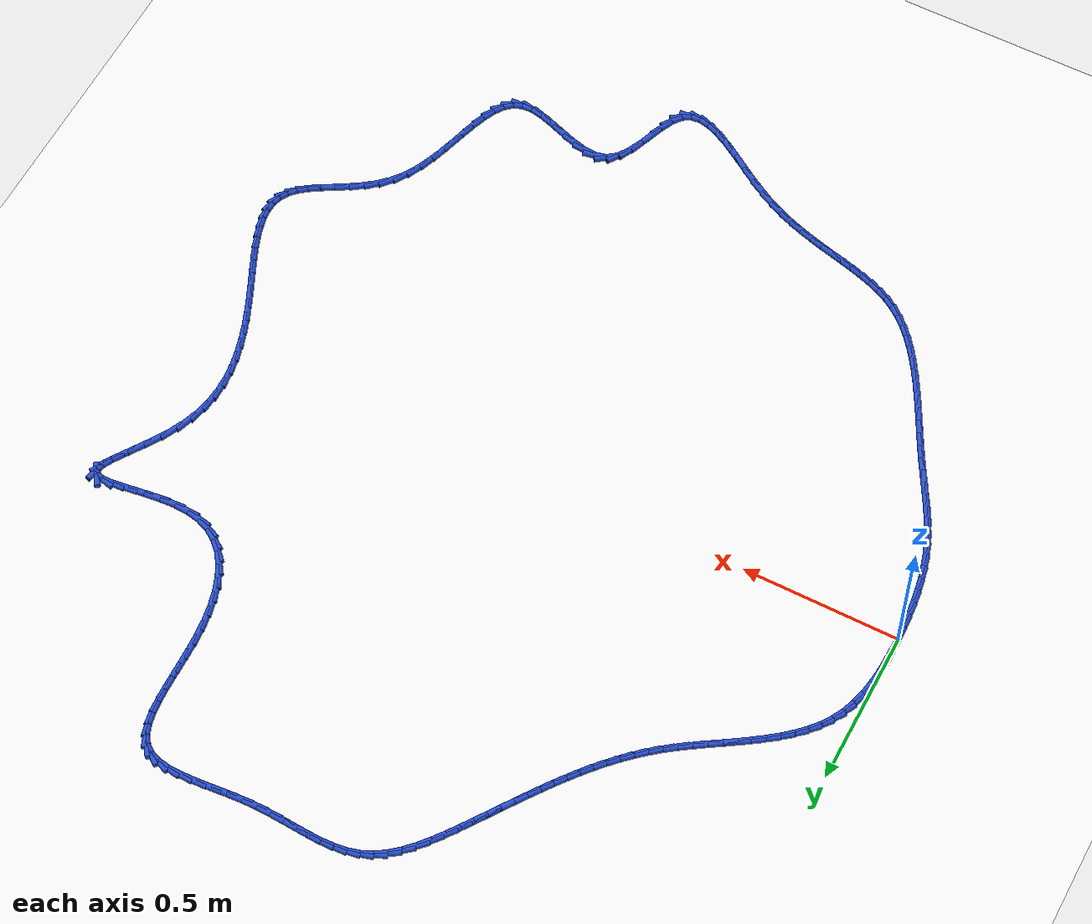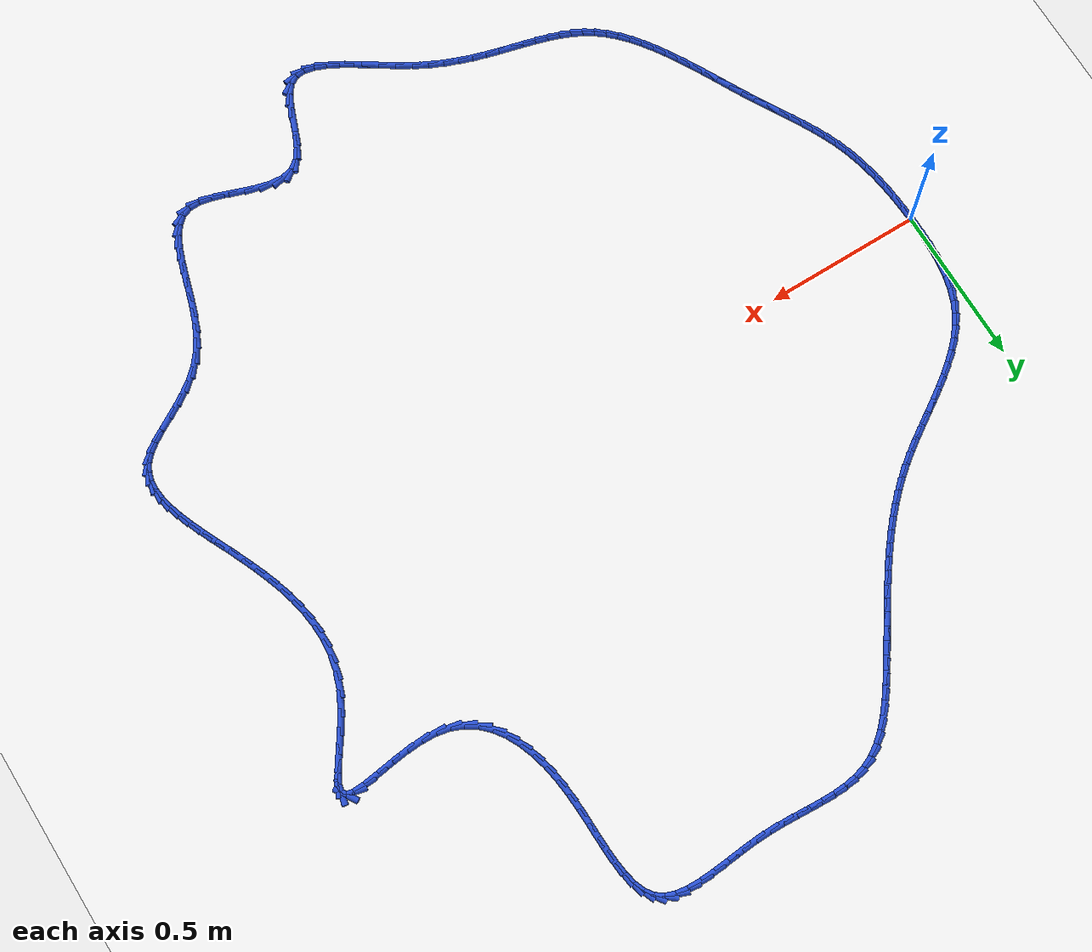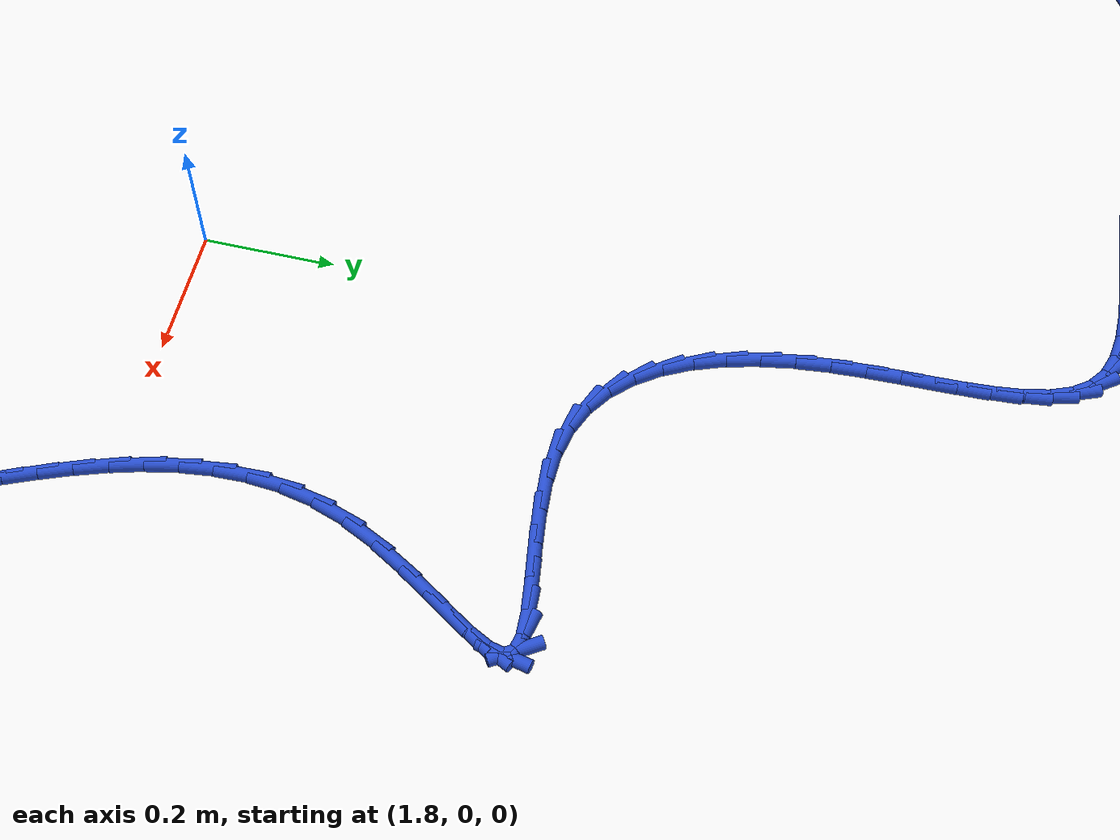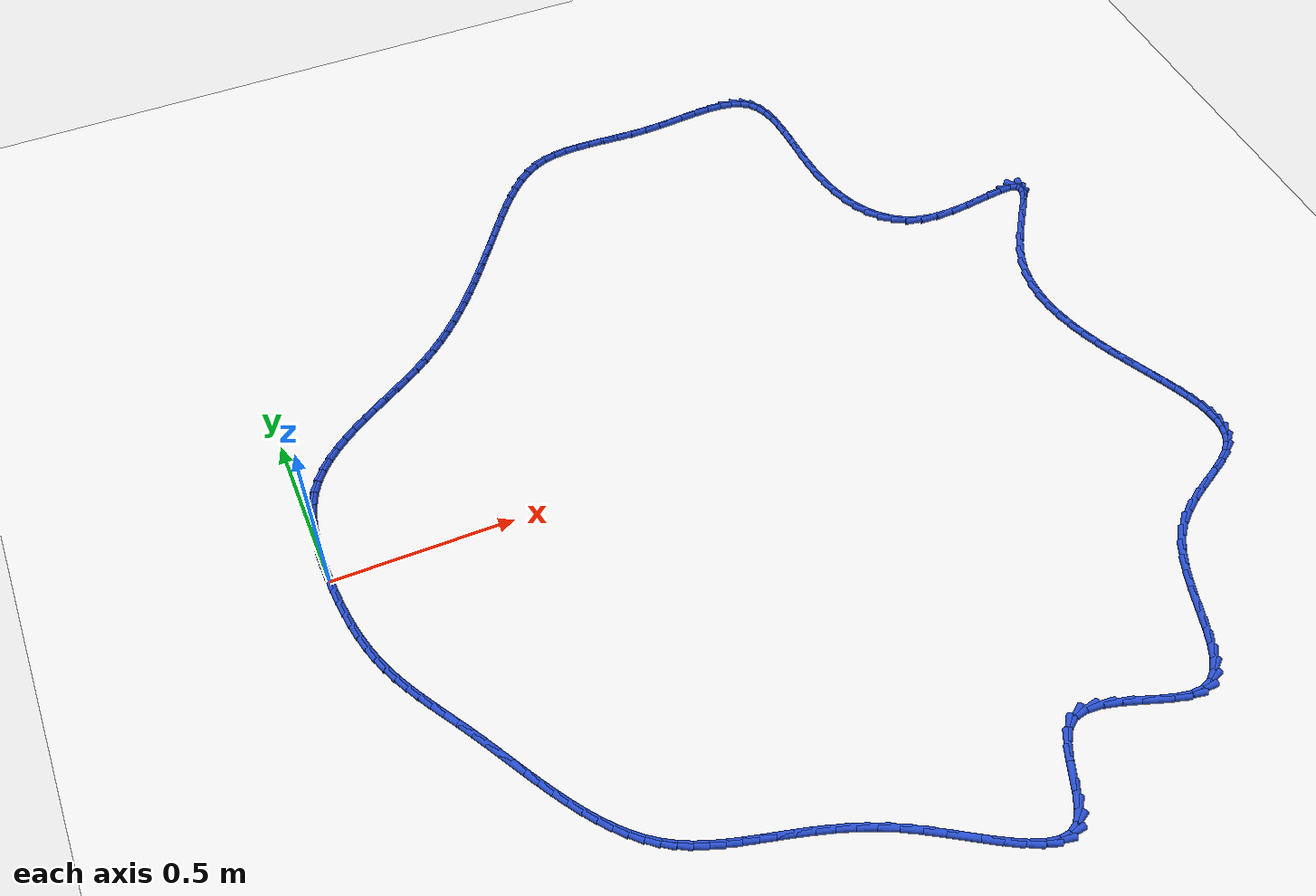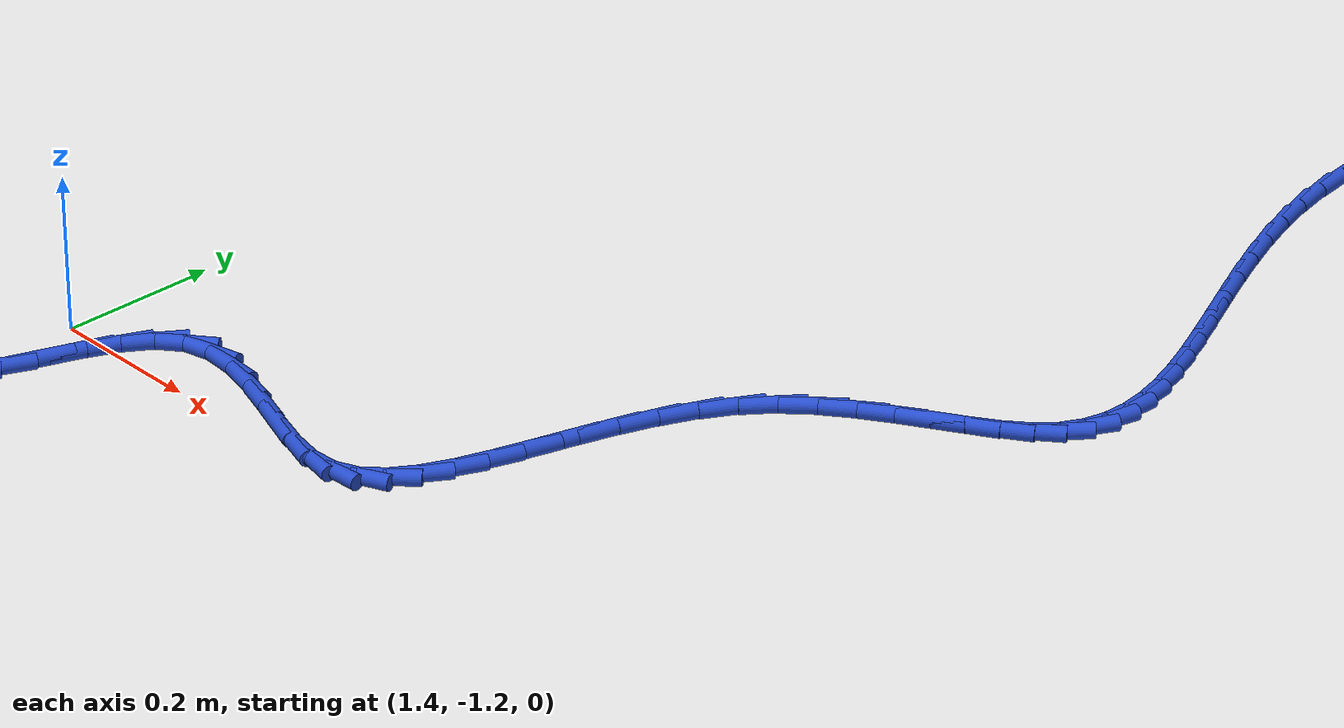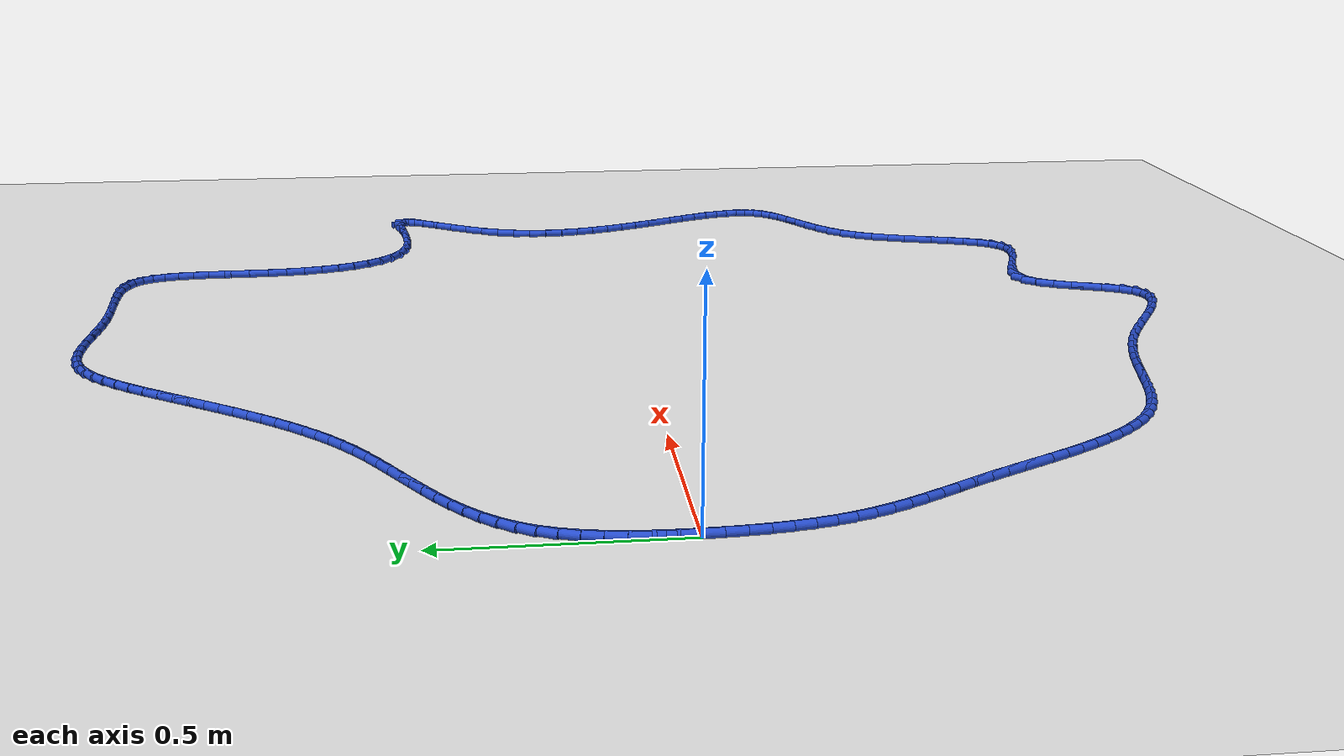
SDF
<sdf version="1.6">
 <world name="default">
  <light name="sun" type="directional">
   <pose>0 0 10 0 -0 0</pose>
   <diffuse>0.8 0.8 0.8 1</diffuse>
   <specular>0.2 0.2 0.2 1</specular>
   <attenuation>
    <range>1000</range>
    <constant>0.9</constant>
    <linear>0.01</linear>
    <quadratic>0.001</quadratic>
   </attenuation>
   <direction>-0.5 0.1 -0.9</direction>
  </light>
  <model name="ground_plane">
   <static>1</static>
   <link name="link">
    <collision name="collision">
     <geometry><plane><normal>0 0 1</normal><size>100 100</size></plane></geometry>
     <surface><friction><ode><mu>100</mu><mu2>50</mu2></ode></friction></surface>
    </collision>
    <visual name="visual">
     <cast_shadows>0</cast_shadows>
     <geometry><plane><normal>0 0 1</normal><size>100 100</size></plane></geometry>
     <material>
      <script><uri>file://media/materials/scripts/gazebo.material</uri><name>Gazebo/WhiteGlow</name></script>
     </material>
    </visual>
   </link>
  </model>
  <gravity>0 0 -9.8</gravity>
  <magnetic_field>6e-06 2.3e-05 -4.2e-05</magnetic_field>
  <atmosphere type="adiabatic"/>
  <physics name="default_physics" default="0" type="ode">
   <max_step_size>0.001</max_step_size>
   <real_time_factor>1</real_time_factor>
   <real_time_update_rate>1000</real_time_update_rate>
  </physics>
  <scene><ambient>0.4 0.4 0.4 1</ambient><background>0.7 0.7 0.7 1</background><shadows>1</shadows></scene>
  <spherical_coordinates>
   <surface_model>EARTH_WGS84</surface_model>
   <latitude_deg>0</latitude_deg>
   <longitude_deg>0</longitude_deg>
   <elevation>0</elevation>
   <heading_deg>0</heading_deg>
  </spherical_coordinates>
  <model name="line">
   <link name="link_0">
    <pose>4.423544863740858e-17 4.163336342344337e-17 0.01 0 1.57 -1.556785566252386</pose>
    <collision name="collision">
     <geometry><cylinder><radius>0.01</radius><length>0.08</length></cylinder></geometry>
    </collision>
    <visual name="visual">
     <material>
      <script><name>Gazebo/Blue</name><uri>file://media/materials/scripts/gazebo.material</uri></script>
     </material>
     <geometry><cylinder><radius>0.01</radius><length>0.08</length></cylinder></geometry>
    </visual>
   </link>
   <link name="link_1">
    <pose>-0.00061148497088987 0.043641096907162294 0.01 0 1.57 1.5525097524919338</pose>
    <collision name="collision">
     <geometry><cylinder><radius>0.01</radius><length>0.08</length></cylinder></geometry>
    </collision>
    <visual name="visual">
     <material>
      <script><name>Gazebo/Blue</name><uri>file://media/materials/scripts/gazebo.material</uri></script>
     </material>
     <geometry><cylinder><radius>0.01</radius><length>0.08</length></cylinder></geometry>
    </visual>
   </link>
   <link name="link_2">
    <pose>0.00018691870310016132 0.08729687757461442 0.01 0 1.57 1.5098056811043024</pose>
    <collision name="collision">
     <geometry><cylinder><radius>0.01</radius><length>0.08</length></cylinder></geometry>
    </collision>
    <visual name="visual">
     <material>
      <script><name>Gazebo/Blue</name><uri>file://media/materials/scripts/gazebo.material</uri></script>
     </material>
     <geometry><cylinder><radius>0.01</radius><length>0.08</length></cylinder></geometry>
    </visual>
   </link>
   <link name="link_3">
    <pose>0.002828787985345237 0.13055912945101494 0.01 0 1.57 1.455463689485531</pose>
    <collision name="collision">
     <geometry><cylinder><radius>0.01</radius><length>0.08</length></cylinder></geometry>
    </collision>
    <visual name="visual">
     <material>
      <script><name>Gazebo/Blue</name><uri>file://media/materials/scripts/gazebo.material</uri></script>
     </material>
     <geometry><cylinder><radius>0.01</radius><length>0.08</length></cylinder></geometry>
    </visual>
   </link>
   <link name="link_4">
    <pose>0.007747699839220458 0.1730196399850226 0.01 0 1.57 1.3879072587157146</pose>
    <collision name="collision">
     <geometry><cylinder><radius>0.01</radius><length>0.08</length></cylinder></geometry>
    </collision>
    <visual name="visual">
     <material>
      <script><name>Gazebo/Blue</name><uri>file://media/materials/scripts/gazebo.material</uri></script>
     </material>
     <geometry><cylinder><radius>0.01</radius><length>0.08</length></cylinder></geometry>
    </visual>
   </link>
   <link name="link_5">
    <pose>0.01537723122810092 0.21427019662529592 0.01 0 1.57 1.305368924905771</pose>
    <collision name="collision">
     <geometry><cylinder><radius>0.01</radius><length>0.08</length></cylinder></geometry>
    </collision>
    <visual name="visual">
     <material>
      <script><name>Gazebo/Blue</name><uri>file://media/materials/scripts/gazebo.material</uri></script>
     </material>
     <geometry><cylinder><radius>0.01</radius><length>0.08</length></cylinder></geometry>
    </visual>
   </link>
   <link name="link_6">
    <pose>0.026150959115361715 0.2539025868204936 0.01 0 1.57 1.2062276343844942</pose>
    <collision name="collision">
     <geometry><cylinder><radius>0.01</radius><length>0.08</length></cylinder></geometry>
    </collision>
    <visual name="visual">
     <material>
      <script><name>Gazebo/Blue</name><uri>file://media/materials/scripts/gazebo.material</uri></script>
     </material>
     <geometry><cylinder><radius>0.01</radius><length>0.08</length></cylinder></geometry>
    </visual>
   </link>
   <link name="link_7">
    <pose>0.04050246046437798 0.2915085980192742 0.01 0 1.57 1.0902701578969165</pose>
    <collision name="collision">
     <geometry><cylinder><radius>0.01</radius><length>0.08</length></cylinder></geometry>
    </collision>
    <visual name="visual">
     <material>
      <script><name>Gazebo/Blue</name><uri>file://media/materials/scripts/gazebo.material</uri></script>
     </material>
     <geometry><cylinder><radius>0.01</radius><length>0.08</length></cylinder></geometry>
    </visual>
   </link>
   <link name="link_8">
    <pose>0.05884489795904817 0.32669591441029444 0.01 0 1.57 0.9725746663491354</pose>
    <collision name="collision">
     <geometry><cylinder><radius>0.01</radius><length>0.08</length></cylinder></geometry>
    </collision>
    <visual name="visual">
     <material>
      <script><name>Gazebo/Blue</name><uri>file://media/materials/scripts/gazebo.material</uri></script>
     </material>
     <geometry><cylinder><radius>0.01</radius><length>0.08</length></cylinder></geometry>
    </visual>
   </link>
   <link name="link_9">
    <pose>0.08114645472271136 0.3594187288300855 0.01 0 1.57 0.8695285254505525</pose>
    <collision name="collision">
     <geometry><cylinder><radius>0.01</radius><length>0.08</length></cylinder></geometry>
    </collision>
    <visual name="visual">
     <material>
      <script><name>Gazebo/Blue</name><uri>file://media/materials/scripts/gazebo.material</uri></script>
     </material>
     <geometry><cylinder><radius>0.01</radius><length>0.08</length></cylinder></geometry>
    </visual>
   </link>
   <link name="link_10">
    <pose>0.10694355981670733 0.38996744397625405 0.01 0 1.57 0.7830941370971138</pose>
    <collision name="collision">
     <geometry><cylinder><radius>0.01</radius><length>0.08</length></cylinder></geometry>
    </collision>
    <visual name="visual">
     <material>
      <script><name>Gazebo/Blue</name><uri>file://media/materials/scripts/gazebo.material</uri></script>
     </material>
     <geometry><cylinder><radius>0.01</radius><length>0.08</length></cylinder></geometry>
    </visual>
   </link>
   <link name="link_11">
    <pose>0.13575487387749763 0.41864629894121025 0.01 0 1.57 0.7131475349329565</pose>
    <collision name="collision">
     <geometry><cylinder><radius>0.01</radius><length>0.08</length></cylinder></geometry>
    </collision>
    <visual name="visual">
     <material>
      <script><name>Gazebo/Blue</name><uri>file://media/materials/scripts/gazebo.material</uri></script>
     </material>
     <geometry><cylinder><radius>0.01</radius><length>0.08</length></cylinder></geometry>
    </visual>
   </link>
   <link name="link_12">
    <pose>0.1670990575415438 0.4457595328173646 0.01 0 1.57 0.6587518446635525</pose>
    <collision name="collision">
     <geometry><cylinder><radius>0.01</radius><length>0.08</length></cylinder></geometry>
    </collision>
    <visual name="visual">
     <material>
      <script><name>Gazebo/Blue</name><uri>file://media/materials/scripts/gazebo.material</uri></script>
     </material>
     <geometry><cylinder><radius>0.01</radius><length>0.08</length></cylinder></geometry>
    </visual>
   </link>
   <link name="link_13">
    <pose>0.2004947714453075 0.47161138469712754 0.01 0 1.57 0.6187150680341555</pose>
    <collision name="collision">
     <geometry><cylinder><radius>0.01</radius><length>0.08</length></cylinder></geometry>
    </collision>
    <visual name="visual">
     <material>
      <script><name>Gazebo/Blue</name><uri>file://media/materials/scripts/gazebo.material</uri></script>
     </material>
     <geometry><cylinder><radius>0.01</radius><length>0.08</length></cylinder></geometry>
    </visual>
   </link>
   <link name="link_14">
    <pose>0.2354606762252504 0.49650609367290954 0.01 0 1.57 0.5919343499389832</pose>
    <collision name="collision">
     <geometry><cylinder><radius>0.01</radius><length>0.08</length></cylinder></geometry>
    </collision>
    <visual name="visual">
     <material>
      <script><name>Gazebo/Blue</name><uri>file://media/materials/scripts/gazebo.material</uri></script>
     </material>
     <geometry><cylinder><radius>0.01</radius><length>0.08</length></cylinder></geometry>
    </visual>
   </link>
   <link name="link_15">
    <pose>0.2715154325178338 0.5207478988371207 0.01 0 1.57 0.5775758826778833</pose>
    <collision name="collision">
     <geometry><cylinder><radius>0.01</radius><length>0.08</length></cylinder></geometry>
    </collision>
    <visual name="visual">
     <material>
      <script><name>Gazebo/Blue</name><uri>file://media/materials/scripts/gazebo.material</uri></script>
     </material>
     <geometry><cylinder><radius>0.01</radius><length>0.08</length></cylinder></geometry>
    </visual>
   </link>
   <link name="link_16">
    <pose>0.30817770095951946 0.5446410392821716 0.01 0 1.57 0.5751556409642943</pose>
    <collision name="collision">
     <geometry><cylinder><radius>0.01</radius><length>0.08</length></cylinder></geometry>
    </collision>
    <visual name="visual">
     <material>
      <script><name>Gazebo/Blue</name><uri>file://media/materials/scripts/gazebo.material</uri></script>
     </material>
     <geometry><cylinder><radius>0.01</radius><length>0.08</length></cylinder></geometry>
    </visual>
   </link>
   <link name="link_17">
    <pose>0.34496614218676896 0.5684897541004724 0.01 0 1.57 0.5845682902340378</pose>
    <collision name="collision">
     <geometry><cylinder><radius>0.01</radius><length>0.08</length></cylinder></geometry>
    </collision>
    <visual name="visual">
     <material>
      <script><name>Gazebo/Blue</name><uri>file://media/materials/scripts/gazebo.material</uri></script>
     </material>
     <geometry><cylinder><radius>0.01</radius><length>0.08</length></cylinder></geometry>
    </visual>
   </link>
   <link name="link_18">
    <pose>0.3813994168360437 0.5925982823844337 0.01 0 1.57 0.6060888026734863</pose>
    <collision name="collision">
     <geometry><cylinder><radius>0.01</radius><length>0.08</length></cylinder></geometry>
    </collision>
    <visual name="visual">
     <material>
      <script><name>Gazebo/Blue</name><uri>file://media/materials/scripts/gazebo.material</uri></script>
     </material>
     <geometry><cylinder><radius>0.01</radius><length>0.08</length></cylinder></geometry>
    </visual>
   </link>
   <link name="link_19">
    <pose>0.4169961855438056 0.6172708632264658 0.01 0 1.57 0.6403506833495011</pose>
    <collision name="collision">
     <geometry><cylinder><radius>0.01</radius><length>0.08</length></cylinder></geometry>
    </collision>
    <visual name="visual">
     <material>
      <script><name>Gazebo/Blue</name><uri>file://media/materials/scripts/gazebo.material</uri></script>
     </material>
     <geometry><cylinder><radius>0.01</radius><length>0.08</length></cylinder></geometry>
    </visual>
   </link>
   <link name="link_20">
    <pose>0.4512751258212564 0.6428117261935644 0.01 0 1.57 0.6850768095033232</pose>
    <collision name="collision">
     <geometry><cylinder><radius>0.01</radius><length>0.08</length></cylinder></geometry>
    </collision>
    <visual name="visual">
     <material>
      <script><name>Gazebo/Blue</name><uri>file://media/materials/scripts/gazebo.material</uri></script>
     </material>
     <geometry><cylinder><radius>0.01</radius><length>0.08</length></cylinder></geometry>
    </visual>
   </link>
   <link name="link_21">
    <pose>0.48388112932498306 0.669453855780227 0.01 0 1.57 0.7297223873508099</pose>
    <collision name="collision">
     <geometry><cylinder><radius>0.01</radius><length>0.08</length></cylinder></geometry>
    </collision>
    <visual name="visual">
     <material>
      <script><name>Gazebo/Blue</name><uri>file://media/materials/scripts/gazebo.material</uri></script>
     </material>
     <geometry><cylinder><radius>0.01</radius><length>0.08</length></cylinder></geometry>
    </visual>
   </link>
   <link name="link_22">
    <pose>0.5148888054719619 0.6971876703811003 0.01 0 1.57 0.7714979246180685</pose>
    <collision name="collision">
     <geometry><cylinder><radius>0.01</radius><length>0.08</length></cylinder></geometry>
    </collision>
    <visual name="visual">
     <material>
      <script><name>Gazebo/Blue</name><uri>file://media/materials/scripts/gazebo.material</uri></script>
     </material>
     <geometry><cylinder><radius>0.01</radius><length>0.08</length></cylinder></geometry>
    </visual>
   </link>
   <link name="link_23">
    <pose>0.5444641343517383 0.7259520116822805 0.01 0 1.57 0.8099397963355663</pose>
    <collision name="collision">
     <geometry><cylinder><radius>0.01</radius><length>0.08</length></cylinder></geometry>
    </collision>
    <visual name="visual">
     <material>
      <script><name>Gazebo/Blue</name><uri>file://media/materials/scripts/gazebo.material</uri></script>
     </material>
     <geometry><cylinder><radius>0.01</radius><length>0.08</length></cylinder></geometry>
    </visual>
   </link>
   <link name="link_24">
    <pose>0.5727730960538581 0.7556857213698646 0.01 0 1.57 0.8446772178276227</pose>
    <collision name="collision">
     <geometry><cylinder><radius>0.01</radius><length>0.08</length></cylinder></geometry>
    </collision>
    <visual name="visual">
     <material>
      <script><name>Gazebo/Blue</name><uri>file://media/materials/scripts/gazebo.material</uri></script>
     </material>
     <geometry><cylinder><radius>0.01</radius><length>0.08</length></cylinder></geometry>
    </visual>
   </link>
   <link name="link_25">
    <pose>0.5999816706678666 0.7863276411299488 0.01 0 1.57 0.8754331827966756</pose>
    <collision name="collision">
     <geometry><cylinder><radius>0.01</radius><length>0.08</length></cylinder></geometry>
    </collision>
    <visual name="visual">
     <material>
      <script><name>Gazebo/Blue</name><uri>file://media/materials/scripts/gazebo.material</uri></script>
     </material>
     <geometry><cylinder><radius>0.01</radius><length>0.08</length></cylinder></geometry>
    </visual>
   </link>
   <link name="link_26">
    <pose>0.6262558382833097 0.81781661264863 0.01 0 1.57 0.9020187629937836</pose>
    <collision name="collision">
     <geometry><cylinder><radius>0.01</radius><length>0.08</length></cylinder></geometry>
    </collision>
    <visual name="visual">
     <material>
      <script><name>Gazebo/Blue</name><uri>file://media/materials/scripts/gazebo.material</uri></script>
     </material>
     <geometry><cylinder><radius>0.01</radius><length>0.08</length></cylinder></geometry>
    </visual>
   </link>
   <link name="link_27">
    <pose>0.6517615789897324 0.8500914776120047 0.01 0 1.57 0.9243230417049163</pose>
    <collision name="collision">
     <geometry><cylinder><radius>0.01</radius><length>0.08</length></cylinder></geometry>
    </collision>
    <visual name="visual">
     <material>
      <script><name>Gazebo/Blue</name><uri>file://media/materials/scripts/gazebo.material</uri></script>
     </material>
     <geometry><cylinder><radius>0.01</radius><length>0.08</length></cylinder></geometry>
    </visual>
   </link>
   <link name="link_28">
    <pose>0.6766648728766808 0.8830910777061692 0.01 0 1.57 0.942300937306241</pose>
    <collision name="collision">
     <geometry><cylinder><radius>0.01</radius><length>0.08</length></cylinder></geometry>
    </collision>
    <visual name="visual">
     <material>
      <script><name>Gazebo/Blue</name><uri>file://media/materials/scripts/gazebo.material</uri></script>
     </material>
     <geometry><cylinder><radius>0.01</radius><length>0.08</length></cylinder></geometry>
    </visual>
   </link>
   <link name="link_29">
    <pose>0.7011317000337002 0.9167542546172204 0.01 0 1.57 0.9559607906340881</pose>
    <collision name="collision">
     <geometry><cylinder><radius>0.01</radius><length>0.08</length></cylinder></geometry>
    </collision>
    <visual name="visual">
     <material>
      <script><name>Gazebo/Blue</name><uri>file://media/materials/scripts/gazebo.material</uri></script>
     </material>
     <geometry><cylinder><radius>0.01</radius><length>0.08</length></cylinder></geometry>
    </visual>
   </link>
   <link name="link_30">
    <pose>0.7253280405503364 0.9510198500312548 0.01 0 1.57 0.9653530486492283</pose>
    <collision name="collision">
     <geometry><cylinder><radius>0.01</radius><length>0.08</length></cylinder></geometry>
    </collision>
    <visual name="visual">
     <material>
      <script><name>Gazebo/Blue</name><uri>file://media/materials/scripts/gazebo.material</uri></script>
     </material>
     <geometry><cylinder><radius>0.01</radius><length>0.08</length></cylinder></geometry>
    </visual>
   </link>
   <link name="link_31">
    <pose>0.7494198745161348 0.985826705634369 0.01 0 1.57 0.9705608360738294</pose>
    <collision name="collision">
     <geometry><cylinder><radius>0.01</radius><length>0.08</length></cylinder></geometry>
    </collision>
    <visual name="visual">
     <material>
      <script><name>Gazebo/Blue</name><uri>file://media/materials/scripts/gazebo.material</uri></script>
     </material>
     <geometry><cylinder><radius>0.01</radius><length>0.08</length></cylinder></geometry>
    </visual>
   </link>
   <link name="link_32">
    <pose>0.7735731820206411 1.02111366311266 0.01 0 1.57 0.9716927556164991</pose>
    <collision name="collision">
     <geometry><cylinder><radius>0.01</radius><length>0.08</length></cylinder></geometry>
    </collision>
    <visual name="visual">
     <material>
      <script><name>Gazebo/Blue</name><uri>file://media/materials/scripts/gazebo.material</uri></script>
     </material>
     <geometry><cylinder><radius>0.01</radius><length>0.08</length></cylinder></geometry>
    </visual>
   </link>
   <link name="link_33">
    <pose>0.7979539431534008 1.0568195641522236 0.01 0 1.57 0.9688779254207448</pose>
    <collision name="collision">
     <geometry><cylinder><radius>0.01</radius><length>0.08</length></cylinder></geometry>
    </collision>
    <visual name="visual">
     <material>
      <script><name>Gazebo/Blue</name><uri>file://media/materials/scripts/gazebo.material</uri></script>
     </material>
     <geometry><cylinder><radius>0.01</radius><length>0.08</length></cylinder></geometry>
    </visual>
   </link>
   <link name="link_34">
    <pose>0.8227281380039596 1.092883250439157 0.01 0 1.57 0.9621442076169071</pose>
    <collision name="collision">
     <geometry><cylinder><radius>0.01</radius><length>0.08</length></cylinder></geometry>
    </collision>
    <visual name="visual">
     <material>
      <script><name>Gazebo/Blue</name><uri>file://media/materials/scripts/gazebo.material</uri></script>
     </material>
     <geometry><cylinder><radius>0.01</radius><length>0.08</length></cylinder></geometry>
    </visual>
   </link>
   <link name="link_35">
    <pose>0.8480619826033418 1.1292346918011351 0.01 0 1.57 0.9467366835521361</pose>
    <collision name="collision">
     <geometry><cylinder><radius>0.01</radius><length>0.08</length></cylinder></geometry>
    </collision>
    <visual name="visual">
     <material>
      <script><name>Gazebo/Blue</name><uri>file://media/materials/scripts/gazebo.material</uri></script>
     </material>
     <geometry><cylinder><radius>0.01</radius><length>0.08</length></cylinder></geometry>
    </visual>
   </link>
   <link name="link_36">
    <pose>0.874131385462575 1.165439401969273 0.01 0 1.57 0.9157407051295933</pose>
    <collision name="collision">
     <geometry><cylinder><radius>0.01</radius><length>0.08</length></cylinder></geometry>
    </collision>
    <visual name="visual">
     <material>
      <script><name>Gazebo/Blue</name><uri>file://media/materials/scripts/gazebo.material</uri></script>
     </material>
     <geometry><cylinder><radius>0.01</radius><length>0.08</length></cylinder></geometry>
    </visual>
   </link>
   <link name="link_37">
    <pose>0.9011251554934223 1.2005778145203592 0.01 0 1.57 0.8670609290528966</pose>
    <collision name="collision">
     <geometry><cylinder><radius>0.01</radius><length>0.08</length></cylinder></geometry>
    </collision>
    <visual name="visual">
     <material>
      <script><name>Gazebo/Blue</name><uri>file://media/materials/scripts/gazebo.material</uri></script>
     </material>
     <geometry><cylinder><radius>0.01</radius><length>0.08</length></cylinder></geometry>
    </visual>
   </link>
   <link name="link_38">
    <pose>0.9292329956187065 1.2336967464767978 0.01 0 1.57 0.7977326851353342</pose>
    <collision name="collision">
     <geometry><cylinder><radius>0.01</radius><length>0.08</length></cylinder></geometry>
    </collision>
    <visual name="visual">
     <material>
      <script><name>Gazebo/Blue</name><uri>file://media/materials/scripts/gazebo.material</uri></script>
     </material>
     <geometry><cylinder><radius>0.01</radius><length>0.08</length></cylinder></geometry>
    </visual>
   </link>
   <link name="link_39">
    <pose>0.9586446087612505 1.2638430148609943 0.01 0 1.57 0.7035746880100318</pose>
    <collision name="collision">
     <geometry><cylinder><radius>0.01</radius><length>0.08</length></cylinder></geometry>
    </collision>
    <visual name="visual">
     <material>
      <script><name>Gazebo/Blue</name><uri>file://media/materials/scripts/gazebo.material</uri></script>
     </material>
     <geometry><cylinder><radius>0.01</radius><length>0.08</length></cylinder></geometry>
    </visual>
   </link>
   <link name="link_40">
    <pose>0.9895496978438766 1.290063436695354 0.01 0 1.57 0.5797978837305164</pose>
    <collision name="collision">
     <geometry><cylinder><radius>0.01</radius><length>0.08</length></cylinder></geometry>
    </collision>
    <visual name="visual">
     <material>
      <script><name>Gazebo/Blue</name><uri>file://media/materials/scripts/gazebo.material</uri></script>
     </material>
     <geometry><cylinder><radius>0.01</radius><length>0.08</length></cylinder></geometry>
    </visual>
   </link>
   <link name="link_41">
    <pose>1.0221379657894079 1.3114048290022817 0.01 0 1.57 0.4249567502436075</pose>
    <collision name="collision">
     <geometry><cylinder><radius>0.01</radius><length>0.08</length></cylinder></geometry>
    </collision>
    <visual name="visual">
     <material>
      <script><name>Gazebo/Blue</name><uri>file://media/materials/scripts/gazebo.material</uri></script>
     </material>
     <geometry><cylinder><radius>0.01</radius><length>0.08</length></cylinder></geometry>
    </visual>
   </link>
   <link name="link_42">
    <pose>1.056587581494379 1.3269943495894398 0.01 0 1.57 0.269783693750644</pose>
    <collision name="collision">
     <geometry><cylinder><radius>0.01</radius><length>0.08</length></cylinder></geometry>
    </collision>
    <visual name="visual">
     <material>
      <script><name>Gazebo/Blue</name><uri>file://media/materials/scripts/gazebo.material</uri></script>
     </material>
     <geometry><cylinder><radius>0.01</radius><length>0.08</length></cylinder></geometry>
    </visual>
   </link>
   <link name="link_43">
    <pose>1.0929213217393825 1.3370415471232042 0.01 0 1.57 0.14301045735514736</pose>
    <collision name="collision">
     <geometry><cylinder><radius>0.01</radius><length>0.08</length></cylinder></geometry>
    </collision>
    <visual name="visual">
     <material>
      <script><name>Gazebo/Blue</name><uri>file://media/materials/scripts/gazebo.material</uri></script>
     </material>
     <geometry><cylinder><radius>0.01</radius><length>0.08</length></cylinder></geometry>
    </visual>
   </link>
   <link name="link_44">
    <pose>1.131050566667512 1.342531908620407 0.01 0 1.57 0.048561996883894225</pose>
    <collision name="collision">
     <geometry><cylinder><radius>0.01</radius><length>0.08</length></cylinder></geometry>
    </collision>
    <visual name="visual">
     <material>
      <script><name>Gazebo/Blue</name><uri>file://media/materials/scripts/gazebo.material</uri></script>
     </material>
     <geometry><cylinder><radius>0.01</radius><length>0.08</length></cylinder></geometry>
    </visual>
   </link>
   <link name="link_45">
    <pose>1.170884268232478 1.3444678347615822 0.01 0 1.57 -0.014863838716233342</pose>
    <collision name="collision">
     <geometry><cylinder><radius>0.01</radius><length>0.08</length></cylinder></geometry>
    </collision>
    <visual name="visual">
     <material>
      <script><name>Gazebo/Blue</name><uri>file://media/materials/scripts/gazebo.material</uri></script>
     </material>
     <geometry><cylinder><radius>0.01</radius><length>0.08</length></cylinder></geometry>
    </visual>
   </link>
   <link name="link_46">
    <pose>1.2123313783879925 1.343851726227262 0.01 0 1.57 -0.050359275299689324</pose>
    <collision name="collision">
     <geometry><cylinder><radius>0.01</radius><length>0.08</length></cylinder></geometry>
    </collision>
    <visual name="visual">
     <material>
      <script><name>Gazebo/Blue</name><uri>file://media/materials/scripts/gazebo.material</uri></script>
     </material>
     <geometry><cylinder><radius>0.01</radius><length>0.08</length></cylinder></geometry>
    </visual>
   </link>
   <link name="link_47">
    <pose>1.2553008490877655 1.3416859836979806 0.01 0 1.57 -0.06102611117015203</pose>
    <collision name="collision">
     <geometry><cylinder><radius>0.01</radius><length>0.08</length></cylinder></geometry>
    </collision>
    <visual name="visual">
     <material>
      <script><name>Gazebo/Blue</name><uri>file://media/materials/scripts/gazebo.material</uri></script>
     </material>
     <geometry><cylinder><radius>0.01</radius><length>0.08</length></cylinder></geometry>
    </visual>
   </link>
   <link name="link_48">
    <pose>1.2997016322855093 1.3389730078542705 0.01 0 1.57 -0.049320633686030776</pose>
    <collision name="collision">
     <geometry><cylinder><radius>0.01</radius><length>0.08</length></cylinder></geometry>
    </collision>
    <visual name="visual">
     <material>
      <script><name>Gazebo/Blue</name><uri>file://media/materials/scripts/gazebo.material</uri></script>
     </material>
     <geometry><cylinder><radius>0.01</radius><length>0.08</length></cylinder></geometry>
    </visual>
   </link>
   <link name="link_49">
    <pose>1.3454426799349344 1.3367151993766644 0.01 0 1.57 -0.01702827381585976</pose>
    <collision name="collision">
     <geometry><cylinder><radius>0.01</radius><length>0.08</length></cylinder></geometry>
    </collision>
    <visual name="visual">
     <material>
      <script><name>Gazebo/Blue</name><uri>file://media/materials/scripts/gazebo.material</uri></script>
     </material>
     <geometry><cylinder><radius>0.01</radius><length>0.08</length></cylinder></geometry>
    </visual>
   </link>
   <link name="link_50">
    <pose>1.3924329439897525 1.3359149589456965 0.01 0 1.57 0.03264071453201777</pose>
    <collision name="collision">
     <geometry><cylinder><radius>0.01</radius><length>0.08</length></cylinder></geometry>
    </collision>
    <visual name="visual">
     <material>
      <script><name>Gazebo/Blue</name><uri>file://media/materials/scripts/gazebo.material</uri></script>
     </material>
     <geometry><cylinder><radius>0.01</radius><length>0.08</length></cylinder></geometry>
    </visual>
   </link>
   <link name="link_51">
    <pose>1.4405463122286135 1.337485971630666 0.01 0 1.57 0.0739321914490907</pose>
    <collision name="collision">
     <geometry><cylinder><radius>0.01</radius><length>0.08</length></cylinder></geometry>
    </collision>
    <visual name="visual">
     <material>
      <script><name>Gazebo/Blue</name><uri>file://media/materials/scripts/gazebo.material</uri></script>
     </material>
     <geometry><cylinder><radius>0.01</radius><length>0.08</length></cylinder></geometry>
    </visual>
   </link>
   <link name="link_52">
    <pose>1.4891605519703146 1.3410866917770883 0.01 0 1.57 0.09031469338997089</pose>
    <collision name="collision">
     <geometry><cylinder><radius>0.01</radius><length>0.08</length></cylinder></geometry>
    </collision>
    <visual name="visual">
     <material>
      <script><name>Gazebo/Blue</name><uri>file://media/materials/scripts/gazebo.material</uri></script>
     </material>
     <geometry><cylinder><radius>0.01</radius><length>0.08</length></cylinder></geometry>
    </visual>
   </link>
   <link name="link_53">
    <pose>1.537285607584171 1.3454449475933477 0.01 0 1.57 0.08176173282360281</pose>
    <collision name="collision">
     <geometry><cylinder><radius>0.01</radius><length>0.08</length></cylinder></geometry>
    </collision>
    <visual name="visual">
     <material>
      <script><name>Gazebo/Blue</name><uri>file://media/materials/scripts/gazebo.material</uri></script>
     </material>
     <geometry><cylinder><radius>0.01</radius><length>0.08</length></cylinder></geometry>
    </visual>
   </link>
   <link name="link_54">
    <pose>1.5839227410869665 1.3492666001315954 0.01 0 1.57 0.04506321978561428</pose>
    <collision name="collision">
     <geometry><cylinder><radius>0.01</radius><length>0.08</length></cylinder></geometry>
    </collision>
    <visual name="visual">
     <material>
      <script><name>Gazebo/Blue</name><uri>file://media/materials/scripts/gazebo.material</uri></script>
     </material>
     <geometry><cylinder><radius>0.01</radius><length>0.08</length></cylinder></geometry>
    </visual>
   </link>
   <link name="link_55">
    <pose>1.6280732144954837 1.351257510443982 0.01 0 1.57 -0.027878395919522837</pose>
    <collision name="collision">
     <geometry><cylinder><radius>0.01</radius><length>0.08</length></cylinder></geometry>
    </collision>
    <visual name="visual">
     <material>
      <script><name>Gazebo/Blue</name><uri>file://media/materials/scripts/gazebo.material</uri></script>
     </material>
     <geometry><cylinder><radius>0.01</radius><length>0.08</length></cylinder></geometry>
    </visual>
   </link>
   <link name="link_56">
    <pose>1.6687382898265068 1.350123539582658 0.01 0 1.57 -0.1522900121381133</pose>
    <collision name="collision">
     <geometry><cylinder><radius>0.01</radius><length>0.08</length></cylinder></geometry>
    </collision>
    <visual name="visual">
     <material>
      <script><name>Gazebo/Blue</name><uri>file://media/materials/scripts/gazebo.material</uri></script>
     </material>
     <geometry><cylinder><radius>0.01</radius><length>0.08</length></cylinder></geometry>
    </visual>
   </link>
   <link name="link_57">
    <pose>1.7049192290968194 1.3445705485997748 0.01 0 1.57 -0.3517374468548224</pose>
    <collision name="collision">
     <geometry><cylinder><radius>0.01</radius><length>0.08</length></cylinder></geometry>
    </collision>
    <visual name="visual">
     <material>
      <script><name>Gazebo/Blue</name><uri>file://media/materials/scripts/gazebo.material</uri></script>
     </material>
     <geometry><cylinder><radius>0.01</radius><length>0.08</length></cylinder></geometry>
    </visual>
   </link>
   <link name="link_58">
    <pose>1.7356172943232036 1.3333043985474828 0.01 0 1.57 -0.6435152422987169</pose>
    <collision name="collision">
     <geometry><cylinder><radius>0.01</radius><length>0.08</length></cylinder></geometry>
    </collision>
    <visual name="visual">
     <material>
      <script><name>Gazebo/Blue</name><uri>file://media/materials/scripts/gazebo.material</uri></script>
     </material>
     <geometry><cylinder><radius>0.01</radius><length>0.08</length></cylinder></geometry>
    </visual>
   </link>
   <link name="link_59">
    <pose>1.7598941392637613 1.3150962287161942 0.01 0 1.57 -0.9528662296585302</pose>
    <collision name="collision">
     <geometry><cylinder><radius>0.01</radius><length>0.08</length></cylinder></geometry>
    </collision>
    <visual name="visual">
     <material>
      <script><name>Gazebo/Blue</name><uri>file://media/materials/scripts/gazebo.material</uri></script>
     </material>
     <geometry><cylinder><radius>0.01</radius><length>0.08</length></cylinder></geometry>
    </visual>
   </link>
   <link name="link_60">
    <pose>1.7778478101107646 1.2898374287943881 0.01 0 1.57 -1.19001909236368</pose>
    <collision name="collision">
     <geometry><cylinder><radius>0.01</radius><length>0.08</length></cylinder></geometry>
    </collision>
    <visual name="visual">
     <material>
      <script><name>Gazebo/Blue</name><uri>file://media/materials/scripts/gazebo.material</uri></script>
     </material>
     <geometry><cylinder><radius>0.01</radius><length>0.08</length></cylinder></geometry>
    </visual>
   </link>
   <link name="link_61">
    <pose>1.7904480327598677 1.2583615986821408 0.01 0 1.57 -1.350595843162712</pose>
    <collision name="collision">
     <geometry><cylinder><radius>0.01</radius><length>0.08</length></cylinder></geometry>
    </collision>
    <visual name="visual">
     <material>
      <script><name>Gazebo/Blue</name><uri>file://media/materials/scripts/gazebo.material</uri></script>
     </material>
     <geometry><cylinder><radius>0.01</radius><length>0.08</length></cylinder></geometry>
    </visual>
   </link>
   <link name="link_62">
    <pose>1.7986916726410191 1.2215316737639401 0.01 0 1.57 -1.4531477053261797</pose>
    <collision name="collision">
     <geometry><cylinder><radius>0.01</radius><length>0.08</length></cylinder></geometry>
    </collision>
    <visual name="visual">
     <material>
      <script><name>Gazebo/Blue</name><uri>file://media/materials/scripts/gazebo.material</uri></script>
     </material>
     <geometry><cylinder><radius>0.01</radius><length>0.08</length></cylinder></geometry>
    </visual>
   </link>
   <link name="link_63">
    <pose>1.8035755951841685 1.1802105894242738 0.01 0 1.57 -1.5147680551032905</pose>
    <collision name="collision">
     <geometry><cylinder><radius>0.01</radius><length>0.08</length></cylinder></geometry>
    </collision>
    <visual name="visual">
     <material>
      <script><name>Gazebo/Blue</name><uri>file://media/materials/scripts/gazebo.material</uri></script>
     </material>
     <geometry><cylinder><radius>0.01</radius><length>0.08</length></cylinder></geometry>
    </visual>
   </link>
   <link name="link_64">
    <pose>1.8060966658192623 1.1352612810476292 0.01 0 1.57 -1.5465928614473223</pose>
    <collision name="collision">
     <geometry><cylinder><radius>0.01</radius><length>0.08</length></cylinder></geometry>
    </collision>
    <visual name="visual">
     <material>
      <script><name>Gazebo/Blue</name><uri>file://media/materials/scripts/gazebo.material</uri></script>
     </material>
     <geometry><cylinder><radius>0.01</radius><length>0.08</length></cylinder></geometry>
    </visual>
   </link>
   <link name="link_65">
    <pose>1.8072517499762508 1.0875466840184942 0.01 0 1.57 -1.5549570344821428</pose>
    <collision name="collision">
     <geometry><cylinder><radius>0.01</radius><length>0.08</length></cylinder></geometry>
    </collision>
    <visual name="visual">
     <material>
      <script><name>Gazebo/Blue</name><uri>file://media/materials/scripts/gazebo.material</uri></script>
     </material>
     <geometry><cylinder><radius>0.01</radius><length>0.08</length></cylinder></geometry>
    </visual>
   </link>
   <link name="link_66">
    <pose>1.8080377130850822 1.0379297337213569 0.01 0 1.57 -1.542895774640368</pose>
    <collision name="collision">
     <geometry><cylinder><radius>0.01</radius><length>0.08</length></cylinder></geometry>
    </collision>
    <visual name="visual">
     <material>
      <script><name>Gazebo/Blue</name><uri>file://media/materials/scripts/gazebo.material</uri></script>
     </material>
     <geometry><cylinder><radius>0.01</radius><length>0.08</length></cylinder></geometry>
    </visual>
   </link>
   <link name="link_67">
    <pose>1.8094514205757055 0.9872733655407046 0.01 0 1.57 -1.5110966084866622</pose>
    <collision name="collision">
     <geometry><cylinder><radius>0.01</radius><length>0.08</length></cylinder></geometry>
    </collision>
    <visual name="visual">
     <material>
      <script><name>Gazebo/Blue</name><uri>file://media/materials/scripts/gazebo.material</uri></script>
     </material>
     <geometry><cylinder><radius>0.01</radius><length>0.08</length></cylinder></geometry>
    </visual>
   </link>
   <link name="link_68">
    <pose>1.8124897378780687 0.9364405148610253 0.01 0 1.57 -1.4587074859406117</pose>
    <collision name="collision">
     <geometry><cylinder><radius>0.01</radius><length>0.08</length></cylinder></geometry>
    </collision>
    <visual name="visual">
     <material>
      <script><name>Gazebo/Blue</name><uri>file://media/materials/scripts/gazebo.material</uri></script>
     </material>
     <geometry><cylinder><radius>0.01</radius><length>0.08</length></cylinder></geometry>
    </visual>
   </link>
   <link name="link_69">
    <pose>1.818134454134875 0.8862922887702744 0.01 0 1.57 -1.389956284617966</pose>
    <collision name="collision">
     <geometry><cylinder><radius>0.01</radius><length>0.08</length></cylinder></geometry>
    </collision>
    <visual name="visual">
     <material>
      <script><name>Gazebo/Blue</name><uri>file://media/materials/scripts/gazebo.material</uri></script>
     </material>
     <geometry><cylinder><radius>0.01</radius><length>0.08</length></cylinder></geometry>
    </visual>
   </link>
   <link name="link_70">
    <pose>1.8270283308367412 0.837648680581473 0.01 0 1.57 -1.308413541132311</pose>
    <collision name="collision">
     <geometry><cylinder><radius>0.01</radius><length>0.08</length></cylinder></geometry>
    </collision>
    <visual name="visual">
     <material>
      <script><name>Gazebo/Blue</name><uri>file://media/materials/scripts/gazebo.material</uri></script>
     </material>
     <geometry><cylinder><radius>0.01</radius><length>0.08</length></cylinder></geometry>
    </visual>
   </link>
   <link name="link_71">
    <pose>1.8394793398102496 0.7912890837721642 0.01 0 1.57 -1.2107068170605686</pose>
    <collision name="collision">
     <geometry><cylinder><radius>0.01</radius><length>0.08</length></cylinder></geometry>
    </collision>
    <visual name="visual">
     <material>
      <script><name>Gazebo/Blue</name><uri>file://media/materials/scripts/gazebo.material</uri></script>
     </material>
     <geometry><cylinder><radius>0.01</radius><length>0.08</length></cylinder></geometry>
    </visual>
   </link>
   <link name="link_72">
    <pose>1.8557812242343938 0.7479911663163469 0.01 0 1.57 -1.0927134948473172</pose>
    <collision name="collision">
     <geometry><cylinder><radius>0.01</radius><length>0.08</length></cylinder></geometry>
    </collision>
    <visual name="visual">
     <material>
      <script><name>Gazebo/Blue</name><uri>file://media/materials/scripts/gazebo.material</uri></script>
     </material>
     <geometry><cylinder><radius>0.01</radius><length>0.08</length></cylinder></geometry>
    </visual>
   </link>
   <link name="link_73">
    <pose>1.8762277272881676 0.7085325961880219 0.01 0 1.57 -0.9505840917783098</pose>
    <collision name="collision">
     <geometry><cylinder><radius>0.01</radius><length>0.08</length></cylinder></geometry>
    </collision>
    <visual name="visual">
     <material>
      <script><name>Gazebo/Blue</name><uri>file://media/materials/scripts/gazebo.material</uri></script>
     </material>
     <geometry><cylinder><radius>0.01</radius><length>0.08</length></cylinder></geometry>
    </visual>
   </link>
   <link name="link_74">
    <pose>1.901112592150564 0.6736910413611894 0.01 0 1.57 -0.7825182655719428</pose>
    <collision name="collision">
     <geometry><cylinder><radius>0.01</radius><length>0.08</length></cylinder></geometry>
    </collision>
    <visual name="visual">
     <material>
      <script><name>Gazebo/Blue</name><uri>file://media/materials/scripts/gazebo.material</uri></script>
     </material>
     <geometry><cylinder><radius>0.01</radius><length>0.08</length></cylinder></geometry>
    </visual>
   </link>
   <link name="link_75">
    <pose>1.9307295620005764 0.6442441698098494 0.01 0 1.57 -0.591577374526817</pose>
    <collision name="collision">
     <geometry><cylinder><radius>0.01</radius><length>0.08</length></cylinder></geometry>
    </collision>
    <visual name="visual">
     <material>
      <script><name>Gazebo/Blue</name><uri>file://media/materials/scripts/gazebo.material</uri></script>
     </material>
     <geometry><cylinder><radius>0.01</radius><length>0.08</length></cylinder></geometry>
    </visual>
   </link>
   <link name="link_76">
    <pose>1.9653723800171985 0.620969649508002 0.01 0 1.57 -0.3878093489161075</pose>
    <collision name="collision">
     <geometry><cylinder><radius>0.01</radius><length>0.08</length></cylinder></geometry>
    </collision>
    <visual name="visual">
     <material>
      <script><name>Gazebo/Blue</name><uri>file://media/materials/scripts/gazebo.material</uri></script>
     </material>
     <geometry><cylinder><radius>0.01</radius><length>0.08</length></cylinder></geometry>
    </visual>
   </link>
   <link name="link_77">
    <pose>2.005334789379424 0.6046451484296478 0.01 0 1.57 -0.18697481943697516</pose>
    <collision name="collision">
     <geometry><cylinder><radius>0.01</radius><length>0.08</length></cylinder></geometry>
    </collision>
    <visual name="visual">
     <material>
      <script><name>Gazebo/Blue</name><uri>file://media/materials/scripts/gazebo.material</uri></script>
     </material>
     <geometry><cylinder><radius>0.01</radius><length>0.08</length></cylinder></geometry>
    </visual>
   </link>
   <link name="link_78">
    <pose>2.0508895421811517 0.5960268916804057 0.01 0 1.57 -0.026283981945086205</pose>
    <collision name="collision">
     <geometry><cylinder><radius>0.01</radius><length>0.08</length></cylinder></geometry>
    </collision>
    <visual name="visual">
     <material>
      <script><name>Gazebo/Blue</name><uri>file://media/materials/scripts/gazebo.material</uri></script>
     </material>
     <geometry><cylinder><radius>0.01</radius><length>0.08</length></cylinder></geometry>
    </visual>
   </link>
   <link name="link_79">
    <pose>2.101167924670205 0.5947050711765938 0.01 0 1.57 0.07279974871065867</pose>
    <collision name="collision">
     <geometry><cylinder><radius>0.01</radius><length>0.08</length></cylinder></geometry>
    </collision>
    <visual name="visual">
     <material>
      <script><name>Gazebo/Blue</name><uri>file://media/materials/scripts/gazebo.material</uri></script>
     </material>
     <geometry><cylinder><radius>0.01</radius><length>0.08</length></cylinder></geometry>
    </visual>
   </link>
   <link name="link_80">
    <pose>2.1535966578437957 0.5985286268624497 0.01 0 1.57 0.12800280164289157</pose>
    <collision name="collision">
     <geometry><cylinder><radius>0.01</radius><length>0.08</length></cylinder></geometry>
    </collision>
    <visual name="visual">
     <material>
      <script><name>Gazebo/Blue</name><uri>file://media/materials/scripts/gazebo.material</uri></script>
     </material>
     <geometry><cylinder><radius>0.01</radius><length>0.08</length></cylinder></geometry>
    </visual>
   </link>
   <link name="link_81">
    <pose>2.2054631438141317 0.6052041812888639 0.01 0 1.57 0.147791438283808</pose>
    <collision name="collision">
     <geometry><cylinder><radius>0.01</radius><length>0.08</length></cylinder></geometry>
    </collision>
    <visual name="visual">
     <material>
      <script><name>Gazebo/Blue</name><uri>file://media/materials/scripts/gazebo.material</uri></script>
     </material>
     <geometry><cylinder><radius>0.01</radius><length>0.08</length></cylinder></geometry>
    </visual>
   </link>
   <link name="link_82">
    <pose>2.2540547846934245 0.6124383570067274 0.01 0 1.57 0.12837179654970698</pose>
    <collision name="collision">
     <geometry><cylinder><radius>0.01</radius><length>0.08</length></cylinder></geometry>
    </collision>
    <visual name="visual">
     <material>
      <script><name>Gazebo/Blue</name><uri>file://media/materials/scripts/gazebo.material</uri></script>
     </material>
     <geometry><cylinder><radius>0.01</radius><length>0.08</length></cylinder></geometry>
    </visual>
   </link>
   <link name="link_83">
    <pose>2.2966589825938826 0.617937776566931 0.01 0 1.57 0.04336823464539689</pose>
    <collision name="collision">
     <geometry><cylinder><radius>0.01</radius><length>0.08</length></cylinder></geometry>
    </collision>
    <visual name="visual">
     <material>
      <script><name>Gazebo/Blue</name><uri>file://media/materials/scripts/gazebo.material</uri></script>
     </material>
     <geometry><cylinder><radius>0.01</radius><length>0.08</length></cylinder></geometry>
    </visual>
   </link>
   <link name="link_84">
    <pose>2.330563139627714 0.6194090625203653 0.01 0 1.57 -0.2123943496498983</pose>
    <collision name="collision">
     <geometry><cylinder><radius>0.01</radius><length>0.08</length></cylinder></geometry>
    </collision>
    <visual name="visual">
     <material>
      <script><name>Gazebo/Blue</name><uri>file://media/materials/scripts/gazebo.material</uri></script>
     </material>
     <geometry><cylinder><radius>0.01</radius><length>0.08</length></cylinder></geometry>
    </visual>
   </link>
   <link name="link_85">
    <pose>2.353054657907131 0.6145588374179213 0.01 0 1.57 -1.0004877508157324</pose>
    <collision name="collision">
     <geometry><cylinder><radius>0.01</radius><length>0.08</length></cylinder></geometry>
    </collision>
    <visual name="visual">
     <material>
      <script><name>Gazebo/Blue</name><uri>file://media/materials/scripts/gazebo.material</uri></script>
     </material>
     <geometry><cylinder><radius>0.01</radius><length>0.08</length></cylinder></geometry>
    </visual>
   </link>
   <link name="link_86">
    <pose>2.3616142075643625 0.6012138164970053 0.01 0 1.57 1.3543942204053674</pose>
    <collision name="collision">
     <geometry><cylinder><radius>0.01</radius><length>0.08</length></cylinder></geometry>
    </collision>
    <visual name="visual">
     <material>
      <script><name>Gazebo/Blue</name><uri>file://media/materials/scripts/gazebo.material</uri></script>
     </material>
     <geometry><cylinder><radius>0.01</radius><length>0.08</length></cylinder></geometry>
    </visual>
   </link>
   <link name="link_87">
    <pose>2.356748423538991 0.5790809859419566 0.01 0 1.57 1.0931618102962333</pose>
    <collision name="collision">
     <geometry><cylinder><radius>0.01</radius><length>0.08</length></cylinder></geometry>
    </collision>
    <visual name="visual">
     <material>
      <script><name>Gazebo/Blue</name><uri>file://media/materials/scripts/gazebo.material</uri></script>
     </material>
     <geometry><cylinder><radius>0.01</radius><length>0.08</length></cylinder></geometry>
    </visual>
   </link>
   <link name="link_88">
    <pose>2.341363884464642 0.5493586065187686 0.01 0 1.57 1.0045522965104887</pose>
    <collision name="collision">
     <geometry><cylinder><radius>0.01</radius><length>0.08</length></cylinder></geometry>
    </collision>
    <visual name="visual">
     <material>
      <script><name>Gazebo/Blue</name><uri>file://media/materials/scripts/gazebo.material</uri></script>
     </material>
     <geometry><cylinder><radius>0.01</radius><length>0.08</length></cylinder></geometry>
    </visual>
   </link>
   <link name="link_89">
    <pose>2.3184331203912123 0.5132859198176739 0.01 0 1.57 0.9819767871209888</pose>
    <collision name="collision">
     <geometry><cylinder><radius>0.01</radius><length>0.08</length></cylinder></geometry>
    </collision>
    <visual name="visual">
     <material>
      <script><name>Gazebo/Blue</name><uri>file://media/materials/scripts/gazebo.material</uri></script>
     </material>
     <geometry><cylinder><radius>0.01</radius><length>0.08</length></cylinder></geometry>
    </visual>
   </link>
   <link name="link_90">
    <pose>2.2909286613685977 0.47210216742890554 0.01 0 1.57 0.9972425596143414</pose>
    <collision name="collision">
     <geometry><cylinder><radius>0.01</radius><length>0.08</length></cylinder></geometry>
    </collision>
    <visual name="visual">
     <material>
      <script><name>Gazebo/Blue</name><uri>file://media/materials/scripts/gazebo.material</uri></script>
     </material>
     <geometry><cylinder><radius>0.01</radius><length>0.08</length></cylinder></geometry>
    </visual>
   </link>
   <link name="link_91">
    <pose>2.261823037446695 0.42704659094269576 0.01 0 1.57 1.044034522045907</pose>
    <collision name="collision">
     <geometry><cylinder><radius>0.01</radius><length>0.08</length></cylinder></geometry>
    </collision>
    <visual name="visual">
     <material>
      <script><name>Gazebo/Blue</name><uri>file://media/materials/scripts/gazebo.material</uri></script>
     </material>
     <geometry><cylinder><radius>0.01</radius><length>0.08</length></cylinder></geometry>
    </visual>
   </link>
   <link name="link_92">
    <pose>2.2340887786754022 0.3793584319492776 0.01 0 1.57 1.1260745458896164</pose>
    <collision name="collision">
     <geometry><cylinder><radius>0.01</radius><length>0.08</length></cylinder></geometry>
    </collision>
    <visual name="visual">
     <material>
      <script><name>Gazebo/Blue</name><uri>file://media/materials/scripts/gazebo.material</uri></script>
     </material>
     <geometry><cylinder><radius>0.01</radius><length>0.08</length></cylinder></geometry>
    </visual>
   </link>
   <link name="link_93">
    <pose>2.2106984151046136 0.33027693203888364 0.01 0 1.57 1.246651998501154</pose>
    <collision name="collision">
     <geometry><cylinder><radius>0.01</radius><length>0.08</length></cylinder></geometry>
    </collision>
    <visual name="visual">
     <material>
      <script><name>Gazebo/Blue</name><uri>file://media/materials/scripts/gazebo.material</uri></script>
     </material>
     <geometry><cylinder><radius>0.01</radius><length>0.08</length></cylinder></geometry>
    </visual>
   </link>
   <link name="link_94">
    <pose>2.1941019813313622 0.28088207990556296 0.01 0 1.57 1.3749946324505016</pose>
    <collision name="collision">
     <geometry><cylinder><radius>0.01</radius><length>0.08</length></cylinder></geometry>
    </collision>
    <visual name="visual">
     <material>
      <script><name>Gazebo/Blue</name><uri>file://media/materials/scripts/gazebo.material</uri></script>
     </material>
     <geometry><cylinder><radius>0.01</radius><length>0.08</length></cylinder></geometry>
    </visual>
   </link>
   <link name="link_95">
    <pose>2.184309406774296 0.23151013754771846 0.01 0 1.57 1.4959708157244989</pose>
    <collision name="collision">
     <geometry><cylinder><radius>0.01</radius><length>0.08</length></cylinder></geometry>
    </collision>
    <visual name="visual">
     <material>
      <script><name>Gazebo/Blue</name><uri>file://media/materials/scripts/gazebo.material</uri></script>
     </material>
     <geometry><cylinder><radius>0.01</radius><length>0.08</length></cylinder></geometry>
    </visual>
   </link>
   <link name="link_96">
    <pose>2.1806188788242604 0.18228043305812558 0.01 0 1.57 -1.5358975702147402</pose>
    <collision name="collision">
     <geometry><cylinder><radius>0.01</radius><length>0.08</length></cylinder></geometry>
    </collision>
    <visual name="visual">
     <material>
      <script><name>Gazebo/Blue</name><uri>file://media/materials/scripts/gazebo.material</uri></script>
     </material>
     <geometry><cylinder><radius>0.01</radius><length>0.08</length></cylinder></geometry>
    </visual>
   </link>
   <link name="link_97">
    <pose>2.182328500982474 0.13331226896059648 0.01 0 1.57 -1.4396693747408422</pose>
    <collision name="collision">
     <geometry><cylinder><radius>0.01</radius><length>0.08</length></cylinder></geometry>
    </collision>
    <visual name="visual">
     <material>
      <script><name>Gazebo/Blue</name><uri>file://media/materials/scripts/gazebo.material</uri></script>
     </material>
     <geometry><cylinder><radius>0.01</radius><length>0.08</length></cylinder></geometry>
    </visual>
   </link>
   <link name="link_98">
    <pose>2.188736376750155 0.0847249477789446 0.01 0 1.57 -1.357718800722844</pose>
    <collision name="collision">
     <geometry><cylinder><radius>0.01</radius><length>0.08</length></cylinder></geometry>
    </collision>
    <visual name="visual">
     <material>
      <script><name>Gazebo/Blue</name><uri>file://media/materials/scripts/gazebo.material</uri></script>
     </material>
     <geometry><cylinder><radius>0.01</radius><length>0.08</length></cylinder></geometry>
    </visual>
   </link>
   <link name="link_99">
    <pose>2.1991406096285218 0.03663777203698303 0.01 0 1.57 -1.28984036425386</pose>
    <collision name="collision">
     <geometry><cylinder><radius>0.01</radius><length>0.08</length></cylinder></geometry>
    </collision>
    <visual name="visual">
     <material>
      <script><name>Gazebo/Blue</name><uri>file://media/materials/scripts/gazebo.material</uri></script>
     </material>
     <geometry><cylinder><radius>0.01</radius><length>0.08</length></cylinder></geometry>
    </visual>
   </link>
   <link name="link_100">
    <pose>2.212839303118792 -0.010829955741475005 0.01 0 1.57 -1.2353399567506218</pose>
    <collision name="collision">
     <geometry><cylinder><radius>0.01</radius><length>0.08</length></cylinder></geometry>
    </collision>
    <visual name="visual">
     <material>
      <script><name>Gazebo/Blue</name><uri>file://media/materials/scripts/gazebo.material</uri></script>
     </material>
     <geometry><cylinder><radius>0.01</radius><length>0.08</length></cylinder></geometry>
    </visual>
   </link>
   <link name="link_101">
    <pose>2.229130560722183 -0.05755893303261657 0.01 0 1.57 -1.193421910153615</pose>
    <collision name="collision">
     <geometry><cylinder><radius>0.01</radius><length>0.08</length></cylinder></geometry>
    </collision>
    <visual name="visual">
     <material>
      <script><name>Gazebo/Blue</name><uri>file://media/materials/scripts/gazebo.material</uri></script>
     </material>
     <geometry><cylinder><radius>0.01</radius><length>0.08</length></cylinder></geometry>
    </visual>
   </link>
   <link name="link_102">
    <pose>2.2473124859399145 -0.10342985731262856 0.01 0 1.57 -1.1634495268033582</pose>
    <collision name="collision">
     <geometry><cylinder><radius>0.01</radius><length>0.08</length></cylinder></geometry>
    </collision>
    <visual name="visual">
     <material>
      <script><name>Gazebo/Blue</name><uri>file://media/materials/scripts/gazebo.material</uri></script>
     </material>
     <geometry><cylinder><radius>0.01</radius><length>0.08</length></cylinder></geometry>
    </visual>
   </link>
   <link name="link_103">
    <pose>2.266683182273202 -0.14832342605769783 0.01 0 1.57 -1.1451175801470286</pose>
    <collision name="collision">
     <geometry><cylinder><radius>0.01</radius><length>0.08</length></cylinder></geometry>
    </collision>
    <visual name="visual">
     <material>
      <script><name>Gazebo/Blue</name><uri>file://media/materials/scripts/gazebo.material</uri></script>
     </material>
     <geometry><cylinder><radius>0.01</radius><length>0.08</length></cylinder></geometry>
    </visual>
   </link>
   <link name="link_104">
    <pose>2.286540753223266 -0.19212033674401138 0.01 0 1.57 -1.1385859912398966</pose>
    <collision name="collision">
     <geometry><cylinder><radius>0.01</radius><length>0.08</length></cylinder></geometry>
    </collision>
    <visual name="visual">
     <material>
      <script><name>Gazebo/Blue</name><uri>file://media/materials/scripts/gazebo.material</uri></script>
     </material>
     <geometry><cylinder><radius>0.01</radius><length>0.08</length></cylinder></geometry>
    </visual>
   </link>
   <link name="link_105">
    <pose>2.3061833022913225 -0.23470128684775599 0.01 0 1.57 -1.1446191965026153</pose>
    <collision name="collision">
     <geometry><cylinder><radius>0.01</radius><length>0.08</length></cylinder></geometry>
    </collision>
    <visual name="visual">
     <material>
      <script><name>Gazebo/Blue</name><uri>file://media/materials/scripts/gazebo.material</uri></script>
     </material>
     <geometry><cylinder><radius>0.01</radius><length>0.08</length></cylinder></geometry>
    </visual>
   </link>
   <link name="link_106">
    <pose>2.3249089329785906 -0.2759469738451188 0.01 0 1.57 -1.164769670187971</pose>
    <collision name="collision">
     <geometry><cylinder><radius>0.01</radius><length>0.08</length></cylinder></geometry>
    </collision>
    <visual name="visual">
     <material>
      <script><name>Gazebo/Blue</name><uri>file://media/materials/scripts/gazebo.material</uri></script>
     </material>
     <geometry><cylinder><radius>0.01</radius><length>0.08</length></cylinder></geometry>
    </visual>
   </link>
   <link name="link_107">
    <pose>2.3420157487862885 -0.31573809521228663 0.01 0 1.57 -1.201637244671332</pose>
    <collision name="collision">
     <geometry><cylinder><radius>0.01</radius><length>0.08</length></cylinder></geometry>
    </collision>
    <visual name="visual">
     <material>
      <script><name>Gazebo/Blue</name><uri>file://media/materials/scripts/gazebo.material</uri></script>
     </material>
     <geometry><cylinder><radius>0.01</radius><length>0.08</length></cylinder></geometry>
    </visual>
   </link>
   <link name="link_108">
    <pose>2.356801853215633 -0.3539553484254463 0.01 0 1.57 -1.2592121943967765</pose>
    <collision name="collision">
     <geometry><cylinder><radius>0.01</radius><length>0.08</length></cylinder></geometry>
    </collision>
    <visual name="visual">
     <material>
      <script><name>Gazebo/Blue</name><uri>file://media/materials/scripts/gazebo.material</uri></script>
     </material>
     <geometry><cylinder><radius>0.01</radius><length>0.08</length></cylinder></geometry>
    </visual>
   </link>
   <link name="link_109">
    <pose>2.3685653497678434 -0.39047943096078486 0.01 0 1.57 -1.3432147792436566</pose>
    <collision name="collision">
     <geometry><cylinder><radius>0.01</radius><length>0.08</length></cylinder></geometry>
    </collision>
    <visual name="visual">
     <material>
      <script><name>Gazebo/Blue</name><uri>file://media/materials/scripts/gazebo.material</uri></script>
     </material>
     <geometry><cylinder><radius>0.01</radius><length>0.08</length></cylinder></geometry>
    </visual>
   </link>
   <link name="link_110">
    <pose>2.3766043419441365 -0.42519104029448906 0.01 0 1.57 -1.4610315506098177</pose>
    <collision name="collision">
     <geometry><cylinder><radius>0.01</radius><length>0.08</length></cylinder></geometry>
    </collision>
    <visual name="visual">
     <material>
      <script><name>Gazebo/Blue</name><uri>file://media/materials/scripts/gazebo.material</uri></script>
     </material>
     <geometry><cylinder><radius>0.01</radius><length>0.08</length></cylinder></geometry>
    </visual>
   </link>
   <link name="link_111">
    <pose>2.3802169332457317 -0.45797087390274616 0.01 0 1.57 1.5215109387688488</pose>
    <collision name="collision">
     <geometry><cylinder><radius>0.01</radius><length>0.08</length></cylinder></geometry>
    </collision>
    <visual name="visual">
     <material>
      <script><name>Gazebo/Blue</name><uri>file://media/materials/scripts/gazebo.material</uri></script>
     </material>
     <geometry><cylinder><radius>0.01</radius><length>0.08</length></cylinder></geometry>
    </visual>
   </link>
   <link name="link_112">
    <pose>2.3787012271738464 -0.4886996292617428 0.01 0 1.57 1.3190302265714944</pose>
    <collision name="collision">
     <geometry><cylinder><radius>0.01</radius><length>0.08</length></cylinder></geometry>
    </collision>
    <visual name="visual">
     <material>
      <script><name>Gazebo/Blue</name><uri>file://media/materials/scripts/gazebo.material</uri></script>
     </material>
     <geometry><cylinder><radius>0.01</radius><length>0.08</length></cylinder></geometry>
    </visual>
   </link>
   <link name="link_113">
    <pose>2.3713553272296983 -0.5172580038476661 0.01 0 1.57 1.0847587087342372</pose>
    <collision name="collision">
     <geometry><cylinder><radius>0.01</radius><length>0.08</length></cylinder></geometry>
    </collision>
    <visual name="visual">
     <material>
      <script><name>Gazebo/Blue</name><uri>file://media/materials/scripts/gazebo.material</uri></script>
     </material>
     <geometry><cylinder><radius>0.01</radius><length>0.08</length></cylinder></geometry>
    </visual>
   </link>
   <link name="link_114">
    <pose>2.3574773369145055 -0.5435266951367027 0.01 0 1.57 0.8490403589658323</pose>
    <collision name="collision">
     <geometry><cylinder><radius>0.01</radius><length>0.08</length></cylinder></geometry>
    </collision>
    <visual name="visual">
     <material>
      <script><name>Gazebo/Blue</name><uri>file://media/materials/scripts/gazebo.material</uri></script>
     </material>
     <geometry><cylinder><radius>0.01</radius><length>0.08</length></cylinder></geometry>
    </visual>
   </link>
   <link name="link_115">
    <pose>2.336443285600307 -0.5674241533233748 0.01 0 1.57 0.6739334376259184</pose>
    <collision name="collision">
     <geometry><cylinder><radius>0.01</radius><length>0.08</length></cylinder></geometry>
    </collision>
    <visual name="visual">
     <material>
      <script><name>Gazebo/Blue</name><uri>file://media/materials/scripts/gazebo.material</uri></script>
     </material>
     <geometry><cylinder><radius>0.01</radius><length>0.08</length></cylinder></geometry>
    </visual>
   </link>
   <link name="link_116">
    <pose>2.308851555196128 -0.5894610212918614 0.01 0 1.57 0.5759419329419844</pose>
    <collision name="collision">
     <geometry><cylinder><radius>0.01</radius><length>0.08</length></cylinder></geometry>
    </collision>
    <visual name="visual">
     <material>
      <script><name>Gazebo/Blue</name><uri>file://media/materials/scripts/gazebo.material</uri></script>
     </material>
     <geometry><cylinder><radius>0.01</radius><length>0.08</length></cylinder></geometry>
    </visual>
   </link>
   <link name="link_117">
    <pose>2.276271176751166 -0.6106181919627605 0.01 0 1.57 0.5340048891090472</pose>
    <collision name="collision">
     <geometry><cylinder><radius>0.01</radius><length>0.08</length></cylinder></geometry>
    </collision>
    <visual name="visual">
     <material>
      <script><name>Gazebo/Blue</name><uri>file://media/materials/scripts/gazebo.material</uri></script>
     </material>
     <geometry><cylinder><radius>0.01</radius><length>0.08</length></cylinder></geometry>
    </visual>
   </link>
   <link name="link_118">
    <pose>2.240297926096695 -0.631889515291526 0.01 0 1.57 0.5348942899872329</pose>
    <collision name="collision">
     <geometry><cylinder><radius>0.01</radius><length>0.08</length></cylinder></geometry>
    </collision>
    <visual name="visual">
     <material>
      <script><name>Gazebo/Blue</name><uri>file://media/materials/scripts/gazebo.material</uri></script>
     </material>
     <geometry><cylinder><radius>0.01</radius><length>0.08</length></cylinder></geometry>
    </visual>
   </link>
   <link name="link_119">
    <pose>2.2025275790639847 -0.6542688412336124 0.01 0 1.57 0.5726560668674543</pose>
    <collision name="collision">
     <geometry><cylinder><radius>0.01</radius><length>0.08</length></cylinder></geometry>
    </collision>
    <visual name="visual">
     <material>
      <script><name>Gazebo/Blue</name><uri>file://media/materials/scripts/gazebo.material</uri></script>
     </material>
     <geometry><cylinder><radius>0.01</radius><length>0.08</length></cylinder></geometry>
    </visual>
   </link>
   <link name="link_120">
    <pose>2.164555911484307 -0.6787500197444742 0.01 0 1.57 0.6460154613833728</pose>
    <collision name="collision">
     <geometry><cylinder><radius>0.01</radius><length>0.08</length></cylinder></geometry>
    </collision>
    <visual name="visual">
     <material>
      <script><name>Gazebo/Blue</name><uri>file://media/materials/scripts/gazebo.material</uri></script>
     </material>
     <geometry><cylinder><radius>0.01</radius><length>0.08</length></cylinder></geometry>
    </visual>
   </link>
   <link name="link_121">
    <pose>2.1279786991889336 -0.7063269007795656 0.01 0 1.57 0.7559745170893589</pose>
    <collision name="collision">
     <geometry><cylinder><radius>0.01</radius><length>0.08</length></cylinder></geometry>
    </collision>
    <visual name="visual">
     <material>
      <script><name>Gazebo/Blue</name><uri>file://media/materials/scripts/gazebo.material</uri></script>
     </material>
     <geometry><cylinder><radius>0.01</radius><length>0.08</length></cylinder></geometry>
    </visual>
   </link>
   <link name="link_122">
    <pose>2.0943917180091356 -0.737993334294341 0.01 0 1.57 0.9018670380567247</pose>
    <collision name="collision">
     <geometry><cylinder><radius>0.01</radius><length>0.08</length></cylinder></geometry>
    </collision>
    <visual name="visual">
     <material>
      <script><name>Gazebo/Blue</name><uri>file://media/materials/scripts/gazebo.material</uri></script>
     </material>
     <geometry><cylinder><radius>0.01</radius><length>0.08</length></cylinder></geometry>
    </visual>
   </link>
   <link name="link_123">
    <pose>2.0653619085188892 -0.7747160871468728 0.01 0 1.57 1.0488111080520988</pose>
    <collision name="collision">
     <geometry><cylinder><radius>0.01</radius><length>0.08</length></cylinder></geometry>
    </collision>
    <visual name="visual">
     <material>
      <script><name>Gazebo/Blue</name><uri>file://media/materials/scripts/gazebo.material</uri></script>
     </material>
     <geometry><cylinder><radius>0.01</radius><length>0.08</length></cylinder></geometry>
    </visual>
   </link>
   <link name="link_124">
    <pose>2.0413643449102836 -0.8164364065251083 0.01 0 1.57 1.1573748766509249</pose>
    <collision name="collision">
     <geometry><cylinder><radius>0.01</radius><length>0.08</length></cylinder></geometry>
    </collision>
    <visual name="visual">
     <material>
      <script><name>Gazebo/Blue</name><uri>file://media/materials/scripts/gazebo.material</uri></script>
     </material>
     <geometry><cylinder><radius>0.01</radius><length>0.08</length></cylinder></geometry>
    </visual>
   </link>
   <link name="link_125">
    <pose>2.02147233959226 -0.8617789551838699 0.01 0 1.57 1.230766386960012</pose>
    <collision name="collision">
     <geometry><cylinder><radius>0.01</radius><length>0.08</length></cylinder></geometry>
    </collision>
    <visual name="visual">
     <material>
      <script><name>Gazebo/Blue</name><uri>file://media/materials/scripts/gazebo.material</uri></script>
     </material>
     <geometry><cylinder><radius>0.01</radius><length>0.08</length></cylinder></geometry>
    </visual>
   </link>
   <link name="link_126">
    <pose>2.004667175334034 -0.9092819583730446 0.01 0 1.57 1.2740845284288185</pose>
    <collision name="collision">
     <geometry><cylinder><radius>0.01</radius><length>0.08</length></cylinder></geometry>
    </collision>
    <visual name="visual">
     <material>
      <script><name>Gazebo/Blue</name><uri>file://media/materials/scripts/gazebo.material</uri></script>
     </material>
     <geometry><cylinder><radius>0.01</radius><length>0.08</length></cylinder></geometry>
    </visual>
   </link>
   <link name="link_127">
    <pose>1.9899301349048213 -0.9574836413425195 0.01 0 1.57 1.2898919363264685</pose>
    <collision name="collision">
     <geometry><cylinder><radius>0.01</radius><length>0.08</length></cylinder></geometry>
    </collision>
    <visual name="visual">
     <material>
      <script><name>Gazebo/Blue</name><uri>file://media/materials/scripts/gazebo.material</uri></script>
     </material>
     <geometry><cylinder><radius>0.01</radius><length>0.08</length></cylinder></geometry>
    </visual>
   </link>
   <link name="link_128">
    <pose>1.9762425010738383 -1.004922229342182 0.01 0 1.57 1.2774570062393986</pose>
    <collision name="collision">
     <geometry><cylinder><radius>0.01</radius><length>0.08</length></cylinder></geometry>
    </collision>
    <visual name="visual">
     <material>
      <script><name>Gazebo/Blue</name><uri>file://media/materials/scripts/gazebo.material</uri></script>
     </material>
     <geometry><cylinder><radius>0.01</radius><length>0.08</length></cylinder></geometry>
    </visual>
   </link>
   <link name="link_129">
    <pose>1.9625855566103017 -1.0501359476219196 0.01 0 1.57 1.231753026772251</pose>
    <collision name="collision">
     <geometry><cylinder><radius>0.01</radius><length>0.08</length></cylinder></geometry>
    </collision>
    <visual name="visual">
     <material>
      <script><name>Gazebo/Blue</name><uri>file://media/materials/scripts/gazebo.material</uri></script>
     </material>
     <geometry><cylinder><radius>0.01</radius><length>0.08</length></cylinder></geometry>
    </visual>
   </link>
   <link name="link_130">
    <pose>1.9479405842834254 -1.0916630214316188 0.01 0 1.57 1.141530122550871</pose>
    <collision name="collision">
     <geometry><cylinder><radius>0.01</radius><length>0.08</length></cylinder></geometry>
    </collision>
    <visual name="visual">
     <material>
      <script><name>Gazebo/Blue</name><uri>file://media/materials/scripts/gazebo.material</uri></script>
     </material>
     <geometry><cylinder><radius>0.01</radius><length>0.08</length></cylinder></geometry>
    </visual>
   </link>
   <link name="link_131">
    <pose>1.9312888668624275 -1.1280416760211673 0.01 0 1.57 0.9867217538519114</pose>
    <collision name="collision">
     <geometry><cylinder><radius>0.01</radius><length>0.08</length></cylinder></geometry>
    </collision>
    <visual name="visual">
     <material>
      <script><name>Gazebo/Blue</name><uri>file://media/materials/scripts/gazebo.material</uri></script>
     </material>
     <geometry><cylinder><radius>0.01</radius><length>0.08</length></cylinder></geometry>
    </visual>
   </link>
   <link name="link_132">
    <pose>1.9116116871165223 -1.1578101366404516 0.01 0 1.57 0.7408445931452077</pose>
    <collision name="collision">
     <geometry><cylinder><radius>0.01</radius><length>0.08</length></cylinder></geometry>
    </collision>
    <visual name="visual">
     <material>
      <script><name>Gazebo/Blue</name><uri>file://media/materials/scripts/gazebo.material</uri></script>
     </material>
     <geometry><cylinder><radius>0.01</radius><length>0.08</length></cylinder></geometry>
    </visual>
   </link>
   <link name="link_133">
    <pose>1.887890327814927 -1.1795066285393598 0.01 0 1.57 0.3997924974700675</pose>
    <collision name="collision">
     <geometry><cylinder><radius>0.01</radius><length>0.08</length></cylinder></geometry>
    </collision>
    <visual name="visual">
     <material>
      <script><name>Gazebo/Blue</name><uri>file://media/materials/scripts/gazebo.material</uri></script>
     </material>
     <geometry><cylinder><radius>0.01</radius><length>0.08</length></cylinder></geometry>
    </visual>
   </link>
   <link name="link_134">
    <pose>1.8591060717268573 -1.191669376967779 0.01 0 1.57 0.040378917748941756</pose>
    <collision name="collision">
     <geometry><cylinder><radius>0.01</radius><length>0.08</length></cylinder></geometry>
    </collision>
    <visual name="visual">
     <material>
      <script><name>Gazebo/Blue</name><uri>file://media/materials/scripts/gazebo.material</uri></script>
     </material>
     <geometry><cylinder><radius>0.01</radius><length>0.08</length></cylinder></geometry>
    </visual>
   </link>
   <link name="link_135">
    <pose>1.8243736809927054 -1.1930725960288122 0.01 0 1.57 -0.19264231231949314</pose>
    <collision name="collision">
     <geometry><cylinder><radius>0.01</radius><length>0.08</length></cylinder></geometry>
    </collision>
    <visual name="visual">
     <material>
      <script><name>Gazebo/Blue</name><uri>file://media/materials/scripts/gazebo.material</uri></script>
     </material>
     <geometry><cylinder><radius>0.01</radius><length>0.08</length></cylinder></geometry>
    </visual>
   </link>
   <link name="link_136">
    <pose>1.784380933090215 -1.1852715594176126 0.01 0 1.57 -0.30354162155065684</pose>
    <collision name="collision">
     <geometry><cylinder><radius>0.01</radius><length>0.08</length></cylinder></geometry>
    </collision>
    <visual name="visual">
     <material>
      <script><name>Gazebo/Blue</name><uri>file://media/materials/scripts/gazebo.material</uri></script>
     </material>
     <geometry><cylinder><radius>0.01</radius><length>0.08</length></cylinder></geometry>
    </visual>
   </link>
   <link name="link_137">
    <pose>1.7408406691202702 -1.1716338327720202 0.01 0 1.57 -0.3406120776976363</pose>
    <collision name="collision">
     <geometry><cylinder><radius>0.01</radius><length>0.08</length></cylinder></geometry>
    </collision>
    <visual name="visual">
     <material>
      <script><name>Gazebo/Blue</name><uri>file://media/materials/scripts/gazebo.material</uri></script>
     </material>
     <geometry><cylinder><radius>0.01</radius><length>0.08</length></cylinder></geometry>
    </visual>
   </link>
   <link name="link_138">
    <pose>1.6954832794318173 -1.155558008448746 0.01 0 1.57 -0.3211025676102783</pose>
    <collision name="collision">
     <geometry><cylinder><radius>0.01</radius><length>0.08</length></cylinder></geometry>
    </collision>
    <visual name="visual">
     <material>
      <script><name>Gazebo/Blue</name><uri>file://media/materials/scripts/gazebo.material</uri></script>
     </material>
     <geometry><cylinder><radius>0.01</radius><length>0.08</length></cylinder></geometry>
    </visual>
   </link>
   <link name="link_139">
    <pose>1.6500391543738022 -1.140442678804502 0.01 0 1.57 -0.24080839545143007</pose>
    <collision name="collision">
     <geometry><cylinder><radius>0.01</radius><length>0.08</length></cylinder></geometry>
    </collision>
    <visual name="visual">
     <material>
      <script><name>Gazebo/Blue</name><uri>file://media/materials/scripts/gazebo.material</uri></script>
     </material>
     <geometry><cylinder><radius>0.01</radius><length>0.08</length></cylinder></geometry>
    </visual>
   </link>
   <link name="link_140">
    <pose>1.6062386842951706 -1.1296864361959993 0.01 0 1.57 -0.07403776775943223</pose>
    <collision name="collision">
     <geometry><cylinder><radius>0.01</radius><length>0.08</length></cylinder></geometry>
    </collision>
    <visual name="visual">
     <material>
      <script><name>Gazebo/Blue</name><uri>file://media/materials/scripts/gazebo.material</uri></script>
     </material>
     <geometry><cylinder><radius>0.01</radius><length>0.08</length></cylinder></geometry>
    </visual>
   </link>
   <link name="link_141">
    <pose>1.5658122595448687 -1.126687872979949 0.01 0 1.57 0.22697302803071048</pose>
    <collision name="collision">
     <geometry><cylinder><radius>0.01</radius><length>0.08</length></cylinder></geometry>
    </collision>
    <visual name="visual">
     <material>
      <script><name>Gazebo/Blue</name><uri>file://media/materials/scripts/gazebo.material</uri></script>
     </material>
     <geometry><cylinder><radius>0.01</radius><length>0.08</length></cylinder></geometry>
    </visual>
   </link>
   <link name="link_142">
    <pose>1.5304902704718408 -1.134845581513063 0.01 0 1.57 0.6540623513256104</pose>
    <collision name="collision">
     <geometry><cylinder><radius>0.01</radius><length>0.08</length></cylinder></geometry>
    </collision>
    <visual name="visual">
     <material>
      <script><name>Gazebo/Blue</name><uri>file://media/materials/scripts/gazebo.material</uri></script>
     </material>
     <geometry><cylinder><radius>0.01</radius><length>0.08</length></cylinder></geometry>
    </visual>
   </link>
   <link name="link_143">
    <pose>1.5017073337141384 -1.1569115686398688 0.01 0 1.57 0.9740331406166568</pose>
    <collision name="collision">
     <geometry><cylinder><radius>0.01</radius><length>0.08</length></cylinder></geometry>
    </collision>
    <visual name="visual">
     <material>
      <script><name>Gazebo/Blue</name><uri>file://media/materials/scripts/gazebo.material</uri></script>
     </material>
     <geometry><cylinder><radius>0.01</radius><length>0.08</length></cylinder></geometry>
    </visual>
   </link>
   <link name="link_144">
    <pose>1.4786844989627435 -1.1907988028945242 0.01 0 1.57 1.139906556812258</pose>
    <collision name="collision">
     <geometry><cylinder><radius>0.01</radius><length>0.08</length></cylinder></geometry>
    </collision>
    <visual name="visual">
     <material>
      <script><name>Gazebo/Blue</name><uri>file://media/materials/scripts/gazebo.material</uri></script>
     </material>
     <geometry><cylinder><radius>0.01</radius><length>0.08</length></cylinder></geometry>
    </visual>
   </link>
   <link name="link_145">
    <pose>1.4596397790910138 -1.2322275323273464 0.01 0 1.57 1.210090178165145</pose>
    <collision name="collision">
     <geometry><cylinder><radius>0.01</radius><length>0.08</length></cylinder></geometry>
    </collision>
    <visual name="visual">
     <material>
      <script><name>Gazebo/Blue</name><uri>file://media/materials/scripts/gazebo.material</uri></script>
     </material>
     <geometry><cylinder><radius>0.01</radius><length>0.08</length></cylinder></geometry>
    </visual>
   </link>
   <link name="link_146">
    <pose>1.4427862171116066 -1.2769071404668588 0.01 0 1.57 1.2103309697711808</pose>
    <collision name="collision">
     <geometry><cylinder><radius>0.01</radius><length>0.08</length></cylinder></geometry>
    </collision>
    <visual name="visual">
     <material>
      <script><name>Gazebo/Blue</name><uri>file://media/materials/scripts/gazebo.material</uri></script>
     </material>
     <geometry><cylinder><radius>0.01</radius><length>0.08</length></cylinder></geometry>
    </visual>
   </link>
   <link name="link_147">
    <pose>1.4263368560371774 -1.3205470108415858 0.01 0 1.57 1.1351482765720096</pose>
    <collision name="collision">
     <geometry><cylinder><radius>0.01</radius><length>0.08</length></cylinder></geometry>
    </collision>
    <visual name="visual">
     <material>
      <script><name>Gazebo/Blue</name><uri>file://media/materials/scripts/gazebo.material</uri></script>
     </material>
     <geometry><cylinder><radius>0.01</radius><length>0.08</length></cylinder></geometry>
    </visual>
   </link>
   <link name="link_148">
    <pose>1.4085047388803822 -1.3588565269800503 0.01 0 1.57 0.9388739038428346</pose>
    <collision name="collision">
     <geometry><cylinder><radius>0.01</radius><length>0.08</length></cylinder></geometry>
    </collision>
    <visual name="visual">
     <material>
      <script><name>Gazebo/Blue</name><uri>file://media/materials/scripts/gazebo.material</uri></script>
     </material>
     <geometry><cylinder><radius>0.01</radius><length>0.08</length></cylinder></geometry>
    </visual>
   </link>
   <link name="link_149">
    <pose>1.3875029086538768 -1.3875450724107758 0.01 0 1.57 0.5504166617686267</pose>
    <collision name="collision">
     <geometry><cylinder><radius>0.01</radius><length>0.08</length></cylinder></geometry>
    </collision>
    <visual name="visual">
     <material>
      <script><name>Gazebo/Blue</name><uri>file://media/materials/scripts/gazebo.material</uri></script>
     </material>
     <geometry><cylinder><radius>0.01</radius><length>0.08</length></cylinder></geometry>
    </visual>
   </link>
   <link name="link_150">
    <pose>1.361900022455528 -1.4032570168929985 0.01 0 1.57 0.11615054075206706</pose>
    <collision name="collision">
     <geometry><cylinder><radius>0.01</radius><length>0.08</length></cylinder></geometry>
    </collision>
    <visual name="visual">
     <material>
      <script><name>Gazebo/Blue</name><uri>file://media/materials/scripts/gazebo.material</uri></script>
     </material>
     <geometry><cylinder><radius>0.01</radius><length>0.08</length></cylinder></geometry>
    </visual>
   </link>
   <link name="link_151">
    <pose>1.331834848777877 -1.4067648921338576 0.01 0 1.57 -0.19721433773465905</pose>
    <collision name="collision">
     <geometry><cylinder><radius>0.01</radius><length>0.08</length></cylinder></geometry>
    </collision>
    <visual name="visual">
     <material>
      <script><name>Gazebo/Blue</name><uri>file://media/materials/scripts/gazebo.material</uri></script>
     </material>
     <geometry><cylinder><radius>0.01</radius><length>0.08</length></cylinder></geometry>
    </visual>
   </link>
   <link name="link_152">
    <pose>1.2978793506790536 -1.399980191908897 0.01 0 1.57 -0.3864178465983525</pose>
    <collision name="collision">
     <geometry><cylinder><radius>0.01</radius><length>0.08</length></cylinder></geometry>
    </collision>
    <visual name="visual">
     <material>
      <script><name>Gazebo/Blue</name><uri>file://media/materials/scripts/gazebo.material</uri></script>
     </material>
     <geometry><cylinder><radius>0.01</radius><length>0.08</length></cylinder></geometry>
    </visual>
   </link>
   <link name="link_153">
    <pose>1.2606055052177263 -1.3848144468040975 0.01 0 1.57 -0.4956040826320122</pose>
    <collision name="collision">
     <geometry><cylinder><radius>0.01</radius><length>0.08</length></cylinder></geometry>
    </collision>
    <visual name="visual">
     <material>
      <script><name>Gazebo/Blue</name><uri>file://media/materials/scripts/gazebo.material</uri></script>
     </material>
     <geometry><cylinder><radius>0.01</radius><length>0.08</length></cylinder></geometry>
    </visual>
   </link>
   <link name="link_154">
    <pose>1.2205852894525617 -1.3631791874054393 0.01 0 1.57 -0.5555533698530342</pose>
    <collision name="collision">
     <geometry><cylinder><radius>0.01</radius><length>0.08</length></cylinder></geometry>
    </collision>
    <visual name="visual">
     <material>
      <script><name>Gazebo/Blue</name><uri>file://media/materials/scripts/gazebo.material</uri></script>
     </material>
     <geometry><cylinder><radius>0.01</radius><length>0.08</length></cylinder></geometry>
    </visual>
   </link>
   <link name="link_155">
    <pose>1.1783906804422277 -1.3369859442989025 0.01 0 1.57 -0.5823171565447595</pose>
    <collision name="collision">
     <geometry><cylinder><radius>0.01</radius><length>0.08</length></cylinder></geometry>
    </collision>
    <visual name="visual">
     <material>
      <script><name>Gazebo/Blue</name><uri>file://media/materials/scripts/gazebo.material</uri></script>
     </material>
     <geometry><cylinder><radius>0.01</radius><length>0.08</length></cylinder></geometry>
    </visual>
   </link>
   <link name="link_156">
    <pose>1.1345936552453926 -1.3081462480704686 0.01 0 1.57 -0.5831941681795176</pose>
    <collision name="collision">
     <geometry><cylinder><radius>0.01</radius><length>0.08</length></cylinder></geometry>
    </collision>
    <visual name="visual">
     <material>
      <script><name>Gazebo/Blue</name><uri>file://media/materials/scripts/gazebo.material</uri></script>
     </material>
     <geometry><cylinder><radius>0.01</radius><length>0.08</length></cylinder></geometry>
    </visual>
   </link>
   <link name="link_157">
    <pose>1.089766190920723 -1.278571629306117 0.01 0 1.57 -0.560095422615848</pose>
    <collision name="collision">
     <geometry><cylinder><radius>0.01</radius><length>0.08</length></cylinder></geometry>
    </collision>
    <visual name="visual">
     <material>
      <script><name>Gazebo/Blue</name><uri>file://media/materials/scripts/gazebo.material</uri></script>
     </material>
     <geometry><cylinder><radius>0.01</radius><length>0.08</length></cylinder></geometry>
    </visual>
   </link>
   <link name="link_158">
    <pose>1.0444802645268874 -1.2501736185918286 0.01 0 1.57 -0.511260427095678</pose>
    <collision name="collision">
     <geometry><cylinder><radius>0.01</radius><length>0.08</length></cylinder></geometry>
    </collision>
    <visual name="visual">
     <material>
      <script><name>Gazebo/Blue</name><uri>file://media/materials/scripts/gazebo.material</uri></script>
     </material>
     <geometry><cylinder><radius>0.01</radius><length>0.08</length></cylinder></geometry>
    </visual>
   </link>
   <link name="link_159">
    <pose>0.999300970758416 -1.2248273717233324 0.01 0 1.57 -0.44857733694113494</pose>
    <collision name="collision">
     <geometry><cylinder><radius>0.01</radius><length>0.08</length></cylinder></geometry>
    </collision>
    <visual name="visual">
     <material>
      <script><name>Gazebo/Blue</name><uri>file://media/materials/scripts/gazebo.material</uri></script>
     </material>
     <geometry><cylinder><radius>0.01</radius><length>0.08</length></cylinder></geometry>
    </visual>
   </link>
   <link name="link_160">
    <pose>0.9545847750336244 -1.203305393428923 0.01 0 1.57 -0.39109718275592154</pose>
    <collision name="collision">
     <geometry><cylinder><radius>0.01</radius><length>0.08</length></cylinder></geometry>
    </collision>
    <visual name="visual">
     <material>
      <script><name>Gazebo/Blue</name><uri>file://media/materials/scripts/gazebo.material</uri></script>
     </material>
     <geometry><cylinder><radius>0.01</radius><length>0.08</length></cylinder></geometry>
    </visual>
   </link>
   <link name="link_161">
    <pose>0.9104470025127223 -1.1851057097643467 0.01 0 1.57 -0.3415907939661227</pose>
    <collision name="collision">
     <geometry><cylinder><radius>0.01</radius><length>0.08</length></cylinder></geometry>
    </collision>
    <visual name="visual">
     <material>
      <script><name>Gazebo/Blue</name><uri>file://media/materials/scripts/gazebo.material</uri></script>
     </material>
     <geometry><cylinder><radius>0.01</radius><length>0.08</length></cylinder></geometry>
    </visual>
   </link>
   <link name="link_162">
    <pose>0.8669895510167317 -1.169655380379505 0.01 0 1.57 -0.3015587194251946</pose>
    <collision name="collision">
     <geometry><cylinder><radius>0.01</radius><length>0.08</length></cylinder></geometry>
    </collision>
    <visual name="visual">
     <material>
      <script><name>Gazebo/Blue</name><uri>file://media/materials/scripts/gazebo.material</uri></script>
     </material>
     <geometry><cylinder><radius>0.01</radius><length>0.08</length></cylinder></geometry>
    </visual>
   </link>
   <link name="link_163">
    <pose>0.8243143183666753 -1.1563814649242992 0.01 0 1.57 -0.2723191470556252</pose>
    <collision name="collision">
     <geometry><cylinder><radius>0.01</radius><length>0.08</length></cylinder></geometry>
    </collision>
    <visual name="visual">
     <material>
      <script><name>Gazebo/Blue</name><uri>file://media/materials/scripts/gazebo.material</uri></script>
     </material>
     <geometry><cylinder><radius>0.01</radius><length>0.08</length></cylinder></geometry>
    </visual>
   </link>
   <link name="link_164">
    <pose>0.7825232023835749 -1.1447110230486301 0.01 0 1.57 -0.2550699455229081</pose>
    <collision name="collision">
     <geometry><cylinder><radius>0.01</radius><length>0.08</length></cylinder></geometry>
    </collision>
    <visual name="visual">
     <material>
      <script><name>Gazebo/Blue</name><uri>file://media/materials/scripts/gazebo.material</uri></script>
     </material>
     <geometry><cylinder><radius>0.01</radius><length>0.08</length></cylinder></geometry>
    </visual>
   </link>
   <link name="link_165">
    <pose>0.7417181008884532 -1.1340711144024005 0.01 0 1.57 -0.25096538521729544</pose>
    <collision name="collision">
     <geometry><cylinder><radius>0.01</radius><length>0.08</length></cylinder></geometry>
    </collision>
    <visual name="visual">
     <material>
      <script><name>Gazebo/Blue</name><uri>file://media/materials/scripts/gazebo.material</uri></script>
     </material>
     <geometry><cylinder><radius>0.01</radius><length>0.08</length></cylinder></geometry>
    </visual>
   </link>
   <link name="link_166">
    <pose>0.7020009117023325 -1.123888798635511 0.01 0 1.57 -0.2611765017985004</pose>
    <collision name="collision">
     <geometry><cylinder><radius>0.01</radius><length>0.08</length></cylinder></geometry>
    </collision>
    <visual name="visual">
     <material>
      <script><name>Gazebo/Blue</name><uri>file://media/materials/scripts/gazebo.material</uri></script>
     </material>
     <geometry><cylinder><radius>0.01</radius><length>0.08</length></cylinder></geometry>
    </visual>
   </link>
   <link name="link_167">
    <pose>0.6634735326462354 -1.1135911353978627 0.01 0 1.57 -0.2868986312682104</pose>
    <collision name="collision">
     <geometry><cylinder><radius>0.01</radius><length>0.08</length></cylinder></geometry>
    </collision>
    <visual name="visual">
     <material>
      <script><name>Gazebo/Blue</name><uri>file://media/materials/scripts/gazebo.material</uri></script>
     </material>
     <geometry><cylinder><radius>0.01</radius><length>0.08</length></cylinder></geometry>
    </visual>
   </link>
   <link name="link_168">
    <pose>0.6262378615411833 -1.1026051843393578 0.01 0 1.57 -0.32926019871542733</pose>
    <collision name="collision">
     <geometry><cylinder><radius>0.01</radius><length>0.08</length></cylinder></geometry>
    </collision>
    <visual name="visual">
     <material>
      <script><name>Gazebo/Blue</name><uri>file://media/materials/scripts/gazebo.material</uri></script>
     </material>
     <geometry><cylinder><radius>0.01</radius><length>0.08</length></cylinder></geometry>
    </visual>
   </link>
   <link name="link_169">
    <pose>0.590395796208199 -1.090358005109897 0.01 0 1.57 -0.3890787224703426</pose>
    <collision name="collision">
     <geometry><cylinder><radius>0.01</radius><length>0.08</length></cylinder></geometry>
    </collision>
    <visual name="visual">
     <material>
      <script><name>Gazebo/Blue</name><uri>file://media/materials/scripts/gazebo.material</uri></script>
     </material>
     <geometry><cylinder><radius>0.01</radius><length>0.08</length></cylinder></geometry>
    </visual>
   </link>
   <link name="link_170">
    <pose>0.5560492344683047 -1.0762766573593823 0.01 0 1.57 -0.4664255244072326</pose>
    <collision name="collision">
     <geometry><cylinder><radius>0.01</radius><length>0.08</length></cylinder></geometry>
    </collision>
    <visual name="visual">
     <material>
      <script><name>Gazebo/Blue</name><uri>file://media/materials/scripts/gazebo.material</uri></script>
     </material>
     <geometry><cylinder><radius>0.01</radius><length>0.08</length></cylinder></geometry>
    </visual>
   </link>
   <link name="link_171">
    <pose>0.523300074142523 -1.0597882007377148 0.01 0 1.57 -0.5600418412264792</pose>
    <collision name="collision">
     <geometry><cylinder><radius>0.01</radius><length>0.08</length></cylinder></geometry>
    </collision>
    <visual name="visual">
     <material>
      <script><name>Gazebo/Blue</name><uri>file://media/materials/scripts/gazebo.material</uri></script>
     </material>
     <geometry><cylinder><radius>0.01</radius><length>0.08</length></cylinder></geometry>
    </visual>
   </link>
   <link name="link_172">
    <pose>0.49225021305187605 -1.0403196948947961 0.01 0 1.57 -0.6635240244080282</pose>
    <collision name="collision">
     <geometry><cylinder><radius>0.01</radius><length>0.08</length></cylinder></geometry>
    </collision>
    <visual name="visual">
     <material>
      <script><name>Gazebo/Blue</name><uri>file://media/materials/scripts/gazebo.material</uri></script>
     </material>
     <geometry><cylinder><radius>0.01</radius><length>0.08</length></cylinder></geometry>
    </visual>
   </link>
   <link name="link_173">
    <pose>0.4629642484970315 -1.017424891208234 0.01 0 1.57 -0.7578441790830175</pose>
    <collision name="collision">
     <geometry><cylinder><radius>0.01</radius><length>0.08</length></cylinder></geometry>
    </collision>
    <visual name="visual">
     <material>
      <script><name>Gazebo/Blue</name><uri>file://media/materials/scripts/gazebo.material</uri></script>
     </material>
     <geometry><cylinder><radius>0.01</radius><length>0.08</length></cylinder></geometry>
    </visual>
   </link>
   <link name="link_174">
    <pose>0.43532652993200194 -0.9912697553328338 0.01 0 1.57 -0.8379592302786902</pose>
    <collision name="collision">
     <geometry><cylinder><radius>0.01</radius><length>0.08</length></cylinder></geometry>
    </collision>
    <visual name="visual">
     <material>
      <script><name>Gazebo/Blue</name><uri>file://media/materials/scripts/gazebo.material</uri></script>
     </material>
     <geometry><cylinder><radius>0.01</radius><length>0.08</length></cylinder></geometry>
    </visual>
   </link>
   <link name="link_175">
    <pose>0.4091670332242428 -0.9622049335540483 0.01 0 1.57 -0.9047484845513798</pose>
    <collision name="collision">
     <geometry><cylinder><radius>0.01</radius><length>0.08</length></cylinder></geometry>
    </collision>
    <visual name="visual">
     <material>
      <script><name>Gazebo/Blue</name><uri>file://media/materials/scripts/gazebo.material</uri></script>
     </material>
     <geometry><cylinder><radius>0.01</radius><length>0.08</length></cylinder></geometry>
    </visual>
   </link>
   <link name="link_176">
    <pose>0.3843157229802243 -0.9305811104054191 0.01 0 1.57 -0.9594623838422952</pose>
    <collision name="collision">
     <geometry><cylinder><radius>0.01</radius><length>0.08</length></cylinder></geometry>
    </collision>
    <visual name="visual">
     <material>
      <script><name>Gazebo/Blue</name><uri>file://media/materials/scripts/gazebo.material</uri></script>
     </material>
     <geometry><cylinder><radius>0.01</radius><length>0.08</length></cylinder></geometry>
    </visual>
   </link>
   <link name="link_177">
    <pose>0.3606025638064166 -0.8967489704204881 0.01 0 1.57 -1.0034018853895208</pose>
    <collision name="collision">
     <geometry><cylinder><radius>0.01</radius><length>0.08</length></cylinder></geometry>
    </collision>
    <visual name="visual">
     <material>
      <script><name>Gazebo/Blue</name><uri>file://media/materials/scripts/gazebo.material</uri></script>
     </material>
     <geometry><cylinder><radius>0.01</radius><length>0.08</length></cylinder></geometry>
    </visual>
   </link>
   <link name="link_178">
    <pose>0.3378575203092901 -0.8610591981327967 0.01 0 1.57 -1.037744301117872</pose>
    <collision name="collision">
     <geometry><cylinder><radius>0.01</radius><length>0.08</length></cylinder></geometry>
    </collision>
    <visual name="visual">
     <material>
      <script><name>Gazebo/Blue</name><uri>file://media/materials/scripts/gazebo.material</uri></script>
     </material>
     <geometry><cylinder><radius>0.01</radius><length>0.08</length></cylinder></geometry>
    </visual>
   </link>
   <link name="link_179">
    <pose>0.3159105570953151 -0.8238624780758873 0.01 0 1.57 -1.0634646326859907</pose>
    <collision name="collision">
     <geometry><cylinder><radius>0.01</radius><length>0.08</length></cylinder></geometry>
    </collision>
    <visual name="visual">
     <material>
      <script><name>Gazebo/Blue</name><uri>file://media/materials/scripts/gazebo.material</uri></script>
     </material>
     <geometry><cylinder><radius>0.01</radius><length>0.08</length></cylinder></geometry>
    </visual>
   </link>
   <link name="link_180">
    <pose>0.2945916387709618 -0.7855094947833012 0.01 0 1.57 -1.0813094760081126</pose>
    <collision name="collision">
     <geometry><cylinder><radius>0.01</radius><length>0.08</length></cylinder></geometry>
    </collision>
    <visual name="visual">
     <material>
      <script><name>Gazebo/Blue</name><uri>file://media/materials/scripts/gazebo.material</uri></script>
     </material>
     <geometry><cylinder><radius>0.01</radius><length>0.08</length></cylinder></geometry>
    </visual>
   </link>
   <link name="link_181">
    <pose>0.27373072994270053 -0.7463509327885804 0.01 0 1.57 -1.0917950582741758</pose>
    <collision name="collision">
     <geometry><cylinder><radius>0.01</radius><length>0.08</length></cylinder></geometry>
    </collision>
    <visual name="visual">
     <material>
      <script><name>Gazebo/Blue</name><uri>file://media/materials/scripts/gazebo.material</uri></script>
     </material>
     <geometry><cylinder><radius>0.01</radius><length>0.08</length></cylinder></geometry>
    </visual>
   </link>
   <link name="link_182">
    <pose>0.25315779521700144 -0.7067374766252666 0.01 0 1.57 -1.0952129313958823</pose>
    <collision name="collision">
     <geometry><cylinder><radius>0.01</radius><length>0.08</length></cylinder></geometry>
    </collision>
    <visual name="visual">
     <material>
      <script><name>Gazebo/Blue</name><uri>file://media/materials/scripts/gazebo.material</uri></script>
     </material>
     <geometry><cylinder><radius>0.01</radius><length>0.08</length></cylinder></geometry>
    </visual>
   </link>
   <link name="link_183">
    <pose>0.2327027992003351 -0.6670198108269019 0.01 0 1.57 -1.0916346015567677</pose>
    <collision name="collision">
     <geometry><cylinder><radius>0.01</radius><length>0.08</length></cylinder></geometry>
    </collision>
    <visual name="visual">
     <material>
      <script><name>Gazebo/Blue</name><uri>file://media/materials/scripts/gazebo.material</uri></script>
     </material>
     <geometry><cylinder><radius>0.01</radius><length>0.08</length></cylinder></geometry>
    </visual>
   </link>
   <link name="link_184">
    <pose>0.21219570649917152 -0.6275486199270277 0.01 0 1.57 -1.0809109418817002</pose>
    <collision name="collision">
     <geometry><cylinder><radius>0.01</radius><length>0.08</length></cylinder></geometry>
    </collision>
    <visual name="visual">
     <material>
      <script><name>Gazebo/Blue</name><uri>file://media/materials/scripts/gazebo.material</uri></script>
     </material>
     <geometry><cylinder><radius>0.01</radius><length>0.08</length></cylinder></geometry>
    </visual>
   </link>
   <link name="link_185">
    <pose>0.19146648171998104 -0.5886745884591857 0.01 0 1.57 -1.0653908109755392</pose>
    <collision name="collision">
     <geometry><cylinder><radius>0.01</radius><length>0.08</length></cylinder></geometry>
    </collision>
    <visual name="visual">
     <material>
      <script><name>Gazebo/Blue</name><uri>file://media/materials/scripts/gazebo.material</uri></script>
     </material>
     <geometry><cylinder><radius>0.01</radius><length>0.08</length></cylinder></geometry>
    </visual>
   </link>
   <link name="link_186">
    <pose>0.17042838215172032 -0.550654530286171 0.01 0 1.57 -1.0566019737519023</pose>
    <collision name="collision">
     <geometry><cylinder><radius>0.01</radius><length>0.08</length></cylinder></geometry>
    </collision>
    <visual name="visual">
     <material>
      <script><name>Gazebo/Blue</name><uri>file://media/materials/scripts/gazebo.material</uri></script>
     </material>
     <geometry><cylinder><radius>0.01</radius><length>0.08</length></cylinder></geometry>
    </visual>
   </link>
   <link name="link_187">
    <pose>0.14935178444028452 -0.5133427865376174 0.01 0 1.57 -1.058056476572514</pose>
    <collision name="collision">
     <geometry><cylinder><radius>0.01</radius><length>0.08</length></cylinder></geometry>
    </collision>
    <visual name="visual">
     <material>
      <script><name>Gazebo/Blue</name><uri>file://media/materials/scripts/gazebo.material</uri></script>
     </material>
     <geometry><cylinder><radius>0.01</radius><length>0.08</length></cylinder></geometry>
    </visual>
   </link>
   <link name="link_188">
    <pose>0.12860275640929866 -0.4764858545954257 0.01 0 1.57 -1.0701592856821984</pose>
    <collision name="collision">
     <geometry><cylinder><radius>0.01</radius><length>0.08</length></cylinder></geometry>
    </collision>
    <visual name="visual">
     <material>
      <script><name>Gazebo/Blue</name><uri>file://media/materials/scripts/gazebo.material</uri></script>
     </material>
     <geometry><cylinder><radius>0.01</radius><length>0.08</length></cylinder></geometry>
    </visual>
   </link>
   <link name="link_189">
    <pose>0.10854736698822054 -0.43983023059522547 0.01 0 1.57 -1.0932601456238427</pose>
    <collision name="collision">
     <geometry><cylinder><radius>0.01</radius><length>0.08</length></cylinder></geometry>
    </collision>
    <visual name="visual">
     <material>
      <script><name>Gazebo/Blue</name><uri>file://media/materials/scripts/gazebo.material</uri></script>
     </material>
     <geometry><cylinder><radius>0.01</radius><length>0.08</length></cylinder></geometry>
    </visual>
   </link>
   <link name="link_190">
    <pose>0.08955168510650785 -0.40312241067264615 0.01 0 1.57 -1.127601884678907</pose>
    <collision name="collision">
     <geometry><cylinder><radius>0.01</radius><length>0.08</length></cylinder></geometry>
    </collision>
    <visual name="visual">
     <material>
      <script><name>Gazebo/Blue</name><uri>file://media/materials/scripts/gazebo.material</uri></script>
     </material>
     <geometry><cylinder><radius>0.01</radius><length>0.08</length></cylinder></geometry>
    </visual>
   </link>
   <link name="link_191">
    <pose>0.07198177969361852 -0.3661088909633177 0.01 0 1.57 -1.173224530394793</pose>
    <collision name="collision">
     <geometry><cylinder><radius>0.01</radius><length>0.08</length></cylinder></geometry>
    </collision>
    <visual name="visual">
     <material>
      <script><name>Gazebo/Blue</name><uri>file://media/materials/scripts/gazebo.material</uri></script>
     </material>
     <geometry><cylinder><radius>0.01</radius><length>0.08</length></cylinder></geometry>
    </visual>
   </link>
   <link name="link_192">
    <pose>0.05620371967901057 -0.32853616760287024 0.01 0 1.57 -1.2295305946268402</pose>
    <collision name="collision">
     <geometry><cylinder><radius>0.01</radius><length>0.08</length></cylinder></geometry>
    </collision>
    <visual name="visual">
     <material>
      <script><name>Gazebo/Blue</name><uri>file://media/materials/scripts/gazebo.material</uri></script>
     </material>
     <geometry><cylinder><radius>0.01</radius><length>0.08</length></cylinder></geometry>
    </visual>
   </link>
   <link name="link_193">
    <pose>0.04257291454636838 -0.29015700725996774 0.01 0 1.57 -1.2886370725416723</pose>
    <collision name="collision">
     <geometry><cylinder><radius>0.01</radius><length>0.08</length></cylinder></geometry>
    </collision>
    <visual name="visual">
     <material>
      <script><name>Gazebo/Blue</name><uri>file://media/materials/scripts/gazebo.material</uri></script>
     </material>
     <geometry><cylinder><radius>0.01</radius><length>0.08</length></cylinder></geometry>
    </visual>
   </link>
   <link name="link_194">
    <pose>0.031185760442934998 -0.2508765439699757 0.01 0 1.57 -1.342680066871253</pose>
    <collision name="collision">
     <geometry><cylinder><radius>0.01</radius><length>0.08</length></cylinder></geometry>
    </collision>
    <visual name="visual">
     <material>
      <script><name>Gazebo/Blue</name><uri>file://media/materials/scripts/gazebo.material</uri></script>
     </material>
     <geometry><cylinder><radius>0.01</radius><length>0.08</length></cylinder></geometry>
    </visual>
   </link>
   <link name="link_195">
    <pose>0.02187170607810955 -0.2107569464550052 0.01 0 1.57 -1.3911955838176537</pose>
    <collision name="collision">
     <geometry><cylinder><radius>0.01</radius><length>0.08</length></cylinder></geometry>
    </collision>
    <visual name="visual">
     <material>
      <script><name>Gazebo/Blue</name><uri>file://media/materials/scripts/gazebo.material</uri></script>
     </material>
     <geometry><cylinder><radius>0.01</radius><length>0.08</length></cylinder></geometry>
    </visual>
   </link>
   <link name="link_196">
    <pose>0.014447953442374862 -0.1698675877006139 0.01 0 1.57 -1.434208415208118</pose>
    <collision name="collision">
     <geometry><cylinder><radius>0.01</radius><length>0.08</length></cylinder></geometry>
    </collision>
    <visual name="visual">
     <material>
      <script><name>Gazebo/Blue</name><uri>file://media/materials/scripts/gazebo.material</uri></script>
     </material>
     <geometry><cylinder><radius>0.01</radius><length>0.08</length></cylinder></geometry>
    </visual>
   </link>
   <link name="link_197">
    <pose>0.008731704526213748 -0.1282778406923599 0.01 0 1.57 -1.4718437408153324</pose>
    <collision name="collision">
     <geometry><cylinder><radius>0.01</radius><length>0.08</length></cylinder></geometry>
    </collision>
    <visual name="visual">
     <material>
      <script><name>Gazebo/Blue</name><uri>file://media/materials/scripts/gazebo.material</uri></script>
     </material>
     <geometry><cylinder><radius>0.01</radius><length>0.08</length></cylinder></geometry>
    </visual>
   </link>
   <link name="link_198">
    <pose>0.004540161320109032 -0.08605707841580099 0.01 0 1.57 -1.5042869169994215</pose>
    <collision name="collision">
     <geometry><cylinder><radius>0.01</radius><length>0.08</length></cylinder></geometry>
    </collision>
    <visual name="visual">
     <material>
      <script><name>Gazebo/Blue</name><uri>file://media/materials/scripts/gazebo.material</uri></script>
     </material>
     <geometry><cylinder><radius>0.01</radius><length>0.08</length></cylinder></geometry>
    </visual>
   </link>
   <link name="link_199">
    <pose>0.0016905258145435264 -0.04327467385649509 0.01 0 1.57 -1.53175116495139</pose>
    <collision name="collision">
     <geometry><cylinder><radius>0.01</radius><length>0.08</length></cylinder></geometry>
    </collision>
    <visual name="visual">
     <material>
      <script><name>Gazebo/Blue</name><uri>file://media/materials/scripts/gazebo.material</uri></script>
     </material>
     <geometry><cylinder><radius>0.01</radius><length>0.08</length></cylinder></geometry>
    </visual>
   </link>
   <link name="link_200">
    <pose>5.0523821237824507e-17 -6.938893903907228e-17 0.01 0 1.57 -1.5544533003611622</pose>
    <collision name="collision">
     <geometry><cylinder><radius>0.01</radius><length>0.08</length></cylinder></geometry>
    </collision>
    <visual name="visual">
     <material>
      <script><name>Gazebo/Blue</name><uri>file://media/materials/scripts/gazebo.material</uri></script>
     </material>
     <geometry><cylinder><radius>0.01</radius><length>0.08</length></cylinder></geometry>
    </visual>
   </link>
   <link name="link_201">
    <pose>-0.0007142141330385844 0.04369757016812712 0.01 0 1.57 -1.5544533003611625</pose>
    <collision name="collision">
     <geometry><cylinder><radius>0.01</radius><length>0.08</length></cylinder></geometry>
    </collision>
    <visual name="visual">
     <material>
      <script><name>Gazebo/Blue</name><uri>file://media/materials/scripts/gazebo.material</uri></script>
     </material>
     <geometry><cylinder><radius>0.01</radius><length>0.08</length></cylinder></geometry>
    </visual>
   </link>
  </model>
 </world>
</sdf>
